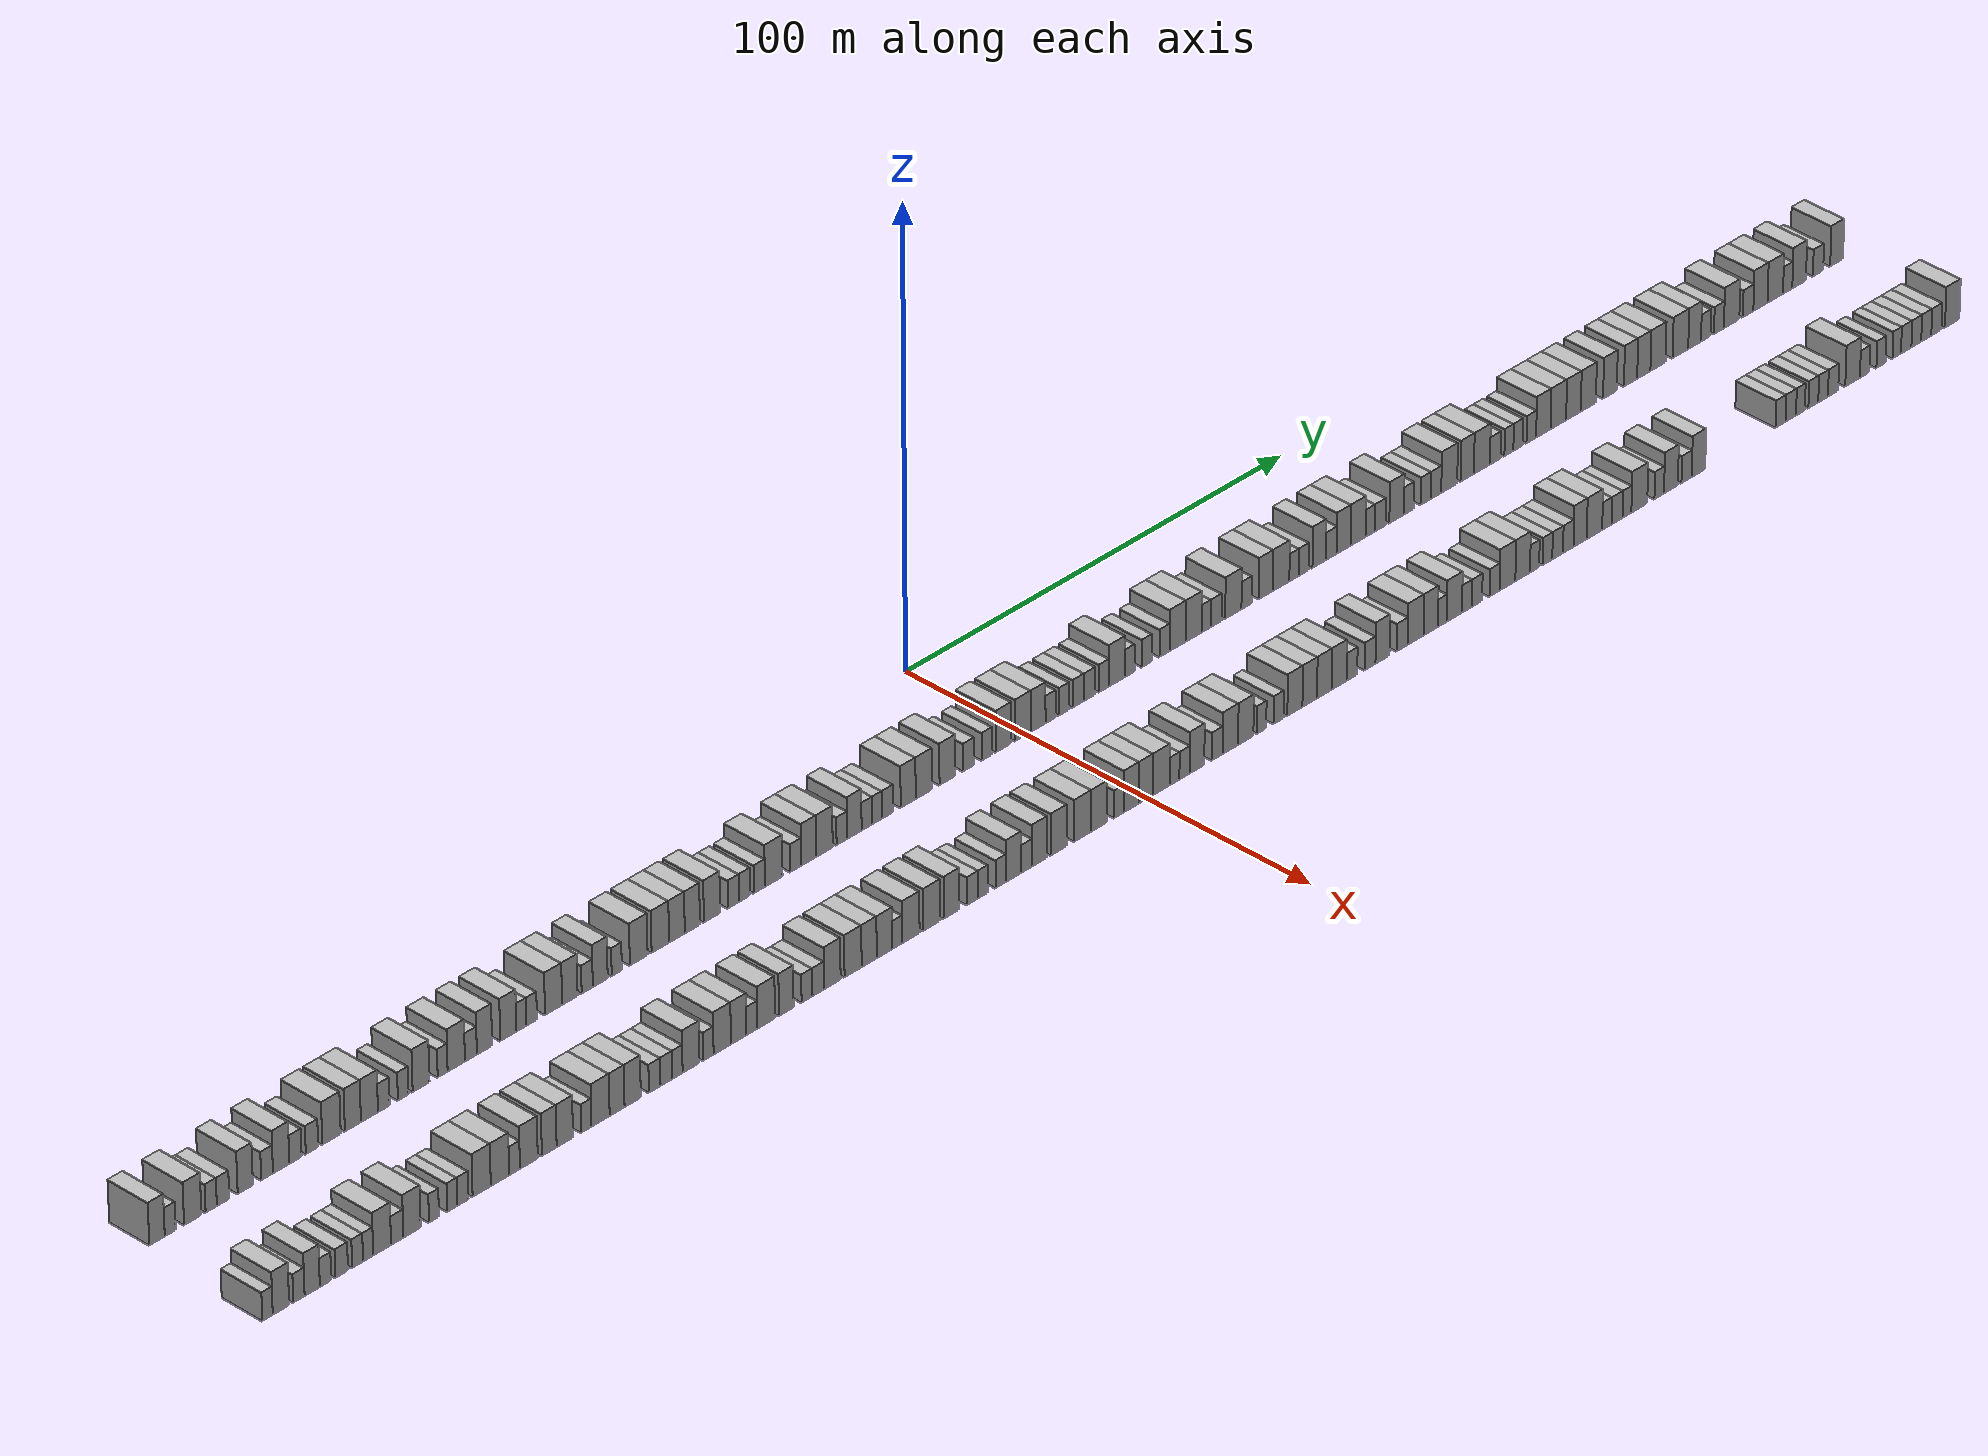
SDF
<sdf version="1.6">
 <world name="default">
  <scene>
   <sky><clouds><speed>12</speed></clouds></sky>
   <ambient>0.4 0.4 0.4 1</ambient>
   <background>0.7 0.7 0.7 1</background>
   <shadows>1</shadows>
  </scene>
  <gravity>0 0 -9.8066</gravity>
  <magnetic_field>6e-06 2.3e-05 -4.2e-05</magnetic_field>
  <physics default="0" name="default_physics" type="ode">
   <ode>
    <solver>
     <type>quick</type>
     <iters>10</iters>
     <sor>1.0</sor>
     <use_dynamic_moi_rescaling>0</use_dynamic_moi_rescaling>
    </solver>
    <constraints>
     <cfm>0</cfm>
     <erp>0.2</erp>
     <contact_max_correcting_vel>100</contact_max_correcting_vel>
     <contact_surface_layer>0.001</contact_surface_layer>
    </constraints>
   </ode>
   <max_step_size>0.004</max_step_size>
   <real_time_factor>1</real_time_factor>
   <real_time_update_rate>250</real_time_update_rate>
  </physics>
  <light name="sun" type="directional">
   <pose>0 0 10 0 0 0</pose>
   <diffuse>0.8 0.8 0.8 1</diffuse>
   <specular>0.2 0.2 0.2 1</specular>
   <attenuation>
    <range>1000</range>
    <constant>0.9</constant>
    <linear>0.01</linear>
    <quadratic>0.001</quadratic>
   </attenuation>
   <direction>-0.5 0.1 -0.9</direction>
  </light>
  <model name="building_1">
   <static>1</static>
   <pose>25.0000 -216.1763 0 0.000000 0.000000 0.000000</pose>
   <link name="link">
    <pose>0 0 4.50 0 0 0</pose>
    <collision name="collision"><geometry><box><size>10.0000 3.6474 9.0000</size></box></geometry></collision>
    <visual name="visual">
     <cast_shadows>0</cast_shadows>
     <geometry><box><size>10.0000 3.6474 9.0000</size></box></geometry>
     <material>
      <script>
       <uri>model://HANNAS_wall/materials/scripts</uri>
       <uri>model://HANNAS_wall/materials/textures</uri>
       <name>vrc/HANNAS_wall</name>
      </script>
     </material>
    </visual>
   </link>
  </model>
  <model name="building_2">
   <static>1</static>
   <pose>25.0000 -213.0599 0 0.000000 0.000000 0.000000</pose>
   <link name="link">
    <pose>0 0 3.00 0 0 0</pose>
    <collision name="collision"><geometry><box><size>10.0000 2.5855 6.0000</size></box></geometry></collision>
    <visual name="visual">
     <cast_shadows>0</cast_shadows>
     <geometry><box><size>10.0000 2.5855 6.0000</size></box></geometry>
     <material>
      <script>
       <uri>model://HANNAS_wall/materials/scripts</uri>
       <uri>model://HANNAS_wall/materials/textures</uri>
       <name>vrc/HANNAS_wall</name>
      </script>
     </material>
    </visual>
   </link>
  </model>
  <model name="building_3">
   <static>1</static>
   <pose>25.0000 -207.7158 0 0.000000 0.000000 0.000000</pose>
   <link name="link">
    <pose>0 0 4.50 0 0 0</pose>
    <collision name="collision"><geometry><box><size>10.0000 4.1027 9.0000</size></box></geometry></collision>
    <visual name="visual">
     <cast_shadows>0</cast_shadows>
     <geometry><box><size>10.0000 4.1027 9.0000</size></box></geometry>
     <material>
      <script>
       <uri>model://HANNAS_wall/materials/scripts</uri>
       <uri>model://HANNAS_wall/materials/textures</uri>
       <name>vrc/HANNAS_wall</name>
      </script>
     </material>
    </visual>
   </link>
  </model>
  <model name="building_4">
   <static>1</static>
   <pose>25.0000 -203.3240 0 0.000000 0.000000 0.000000</pose>
   <link name="link">
    <pose>0 0 3.00 0 0 0</pose>
    <collision name="collision"><geometry><box><size>10.0000 2.6808 6.0000</size></box></geometry></collision>
    <visual name="visual">
     <cast_shadows>0</cast_shadows>
     <geometry><box><size>10.0000 2.6808 6.0000</size></box></geometry>
     <material>
      <script>
       <uri>model://HANNAS_wall/materials/scripts</uri>
       <uri>model://HANNAS_wall/materials/textures</uri>
       <name>vrc/HANNAS_wall</name>
      </script>
     </material>
    </visual>
   </link>
  </model>
  <model name="building_5">
   <static>1</static>
   <pose>25.0000 -200.5025 0 0.000000 0.000000 0.000000</pose>
   <link name="link">
    <pose>0 0 3.00 0 0 0</pose>
    <collision name="collision"><geometry><box><size>10.0000 2.9622 6.0000</size></box></geometry></collision>
    <visual name="visual">
     <cast_shadows>0</cast_shadows>
     <geometry><box><size>10.0000 2.9622 6.0000</size></box></geometry>
     <material>
      <script>
       <uri>model://HANNAS_wall/materials/scripts</uri>
       <uri>model://HANNAS_wall/materials/textures</uri>
       <name>vrc/HANNAS_wall</name>
      </script>
     </material>
    </visual>
   </link>
  </model>
  <model name="building_6">
   <static>1</static>
   <pose>25.0000 -195.2018 0 0.000000 0.000000 0.000000</pose>
   <link name="link">
    <pose>0 0 4.50 0 0 0</pose>
    <collision name="collision"><geometry><box><size>10.0000 3.6391 9.0000</size></box></geometry></collision>
    <visual name="visual">
     <cast_shadows>0</cast_shadows>
     <geometry><box><size>10.0000 3.6391 9.0000</size></box></geometry>
     <material>
      <script>
       <uri>model://HANNAS_wall/materials/scripts</uri>
       <uri>model://HANNAS_wall/materials/textures</uri>
       <name>vrc/HANNAS_wall</name>
      </script>
     </material>
    </visual>
   </link>
  </model>
  <model name="building_7">
   <static>1</static>
   <pose>25.0000 -189.9766 0 0.000000 0.000000 0.000000</pose>
   <link name="link">
    <pose>0 0 3.00 0 0 0</pose>
    <collision name="collision"><geometry><box><size>10.0000 2.8114 6.0000</size></box></geometry></collision>
    <visual name="visual">
     <cast_shadows>0</cast_shadows>
     <geometry><box><size>10.0000 2.8114 6.0000</size></box></geometry>
     <material>
      <script>
       <uri>model://HANNAS_wall/materials/scripts</uri>
       <uri>model://HANNAS_wall/materials/textures</uri>
       <name>vrc/HANNAS_wall</name>
      </script>
     </material>
    </visual>
   </link>
  </model>
  <model name="building_8">
   <static>1</static>
   <pose>25.0000 -186.6073 0 0.000000 0.000000 0.000000</pose>
   <link name="link">
    <pose>0 0 4.50 0 0 0</pose>
    <collision name="collision"><geometry><box><size>10.0000 3.9271 9.0000</size></box></geometry></collision>
    <visual name="visual">
     <cast_shadows>0</cast_shadows>
     <geometry><box><size>10.0000 3.9271 9.0000</size></box></geometry>
     <material>
      <script>
       <uri>model://HANNAS_wall/materials/scripts</uri>
       <uri>model://HANNAS_wall/materials/textures</uri>
       <name>vrc/HANNAS_wall</name>
      </script>
     </material>
    </visual>
   </link>
  </model>
  <model name="building_9">
   <static>1</static>
   <pose>25.0000 -183.1718 0 0.000000 0.000000 0.000000</pose>
   <link name="link">
    <pose>0 0 3.00 0 0 0</pose>
    <collision name="collision"><geometry><box><size>10.0000 2.9438 6.0000</size></box></geometry></collision>
    <visual name="visual">
     <cast_shadows>0</cast_shadows>
     <geometry><box><size>10.0000 2.9438 6.0000</size></box></geometry>
     <material>
      <script>
       <uri>model://HANNAS_wall/materials/scripts</uri>
       <uri>model://HANNAS_wall/materials/textures</uri>
       <name>vrc/HANNAS_wall</name>
      </script>
     </material>
    </visual>
   </link>
  </model>
  <model name="building_10">
   <static>1</static>
   <pose>25.0000 -179.2069 0 0.000000 0.000000 0.000000</pose>
   <link name="link">
    <pose>0 0 3.00 0 0 0</pose>
    <collision name="collision"><geometry><box><size>10.0000 2.9862 6.0000</size></box></geometry></collision>
    <visual name="visual">
     <cast_shadows>0</cast_shadows>
     <geometry><box><size>10.0000 2.9862 6.0000</size></box></geometry>
     <material>
      <script>
       <uri>model://HANNAS_wall/materials/scripts</uri>
       <uri>model://HANNAS_wall/materials/textures</uri>
       <name>vrc/HANNAS_wall</name>
      </script>
     </material>
    </visual>
   </link>
  </model>
  <model name="building_11">
   <static>1</static>
   <pose>25.0000 -174.4941 0 0.000000 0.000000 0.000000</pose>
   <link name="link">
    <pose>0 0 4.50 0 0 0</pose>
    <collision name="collision"><geometry><box><size>10.0000 4.4394 9.0000</size></box></geometry></collision>
    <visual name="visual">
     <cast_shadows>0</cast_shadows>
     <geometry><box><size>10.0000 4.4394 9.0000</size></box></geometry>
     <material>
      <script>
       <uri>model://HANNAS_wall/materials/scripts</uri>
       <uri>model://HANNAS_wall/materials/textures</uri>
       <name>vrc/HANNAS_wall</name>
      </script>
     </material>
    </visual>
   </link>
  </model>
  <model name="building_12">
   <static>1</static>
   <pose>25.0000 -169.3286 0 0.000000 0.000000 0.000000</pose>
   <link name="link">
    <pose>0 0 4.50 0 0 0</pose>
    <collision name="collision"><geometry><box><size>10.0000 3.8914 9.0000</size></box></geometry></collision>
    <visual name="visual">
     <cast_shadows>0</cast_shadows>
     <geometry><box><size>10.0000 3.8914 9.0000</size></box></geometry>
     <material>
      <script>
       <uri>model://HANNAS_wall/materials/scripts</uri>
       <uri>model://HANNAS_wall/materials/textures</uri>
       <name>vrc/HANNAS_wall</name>
      </script>
     </material>
    </visual>
   </link>
  </model>
  <model name="building_13">
   <static>1</static>
   <pose>25.0000 -165.3194 0 0.000000 0.000000 0.000000</pose>
   <link name="link">
    <pose>0 0 4.50 0 0 0</pose>
    <collision name="collision"><geometry><box><size>10.0000 4.1270 9.0000</size></box></geometry></collision>
    <visual name="visual">
     <cast_shadows>0</cast_shadows>
     <geometry><box><size>10.0000 4.1270 9.0000</size></box></geometry>
     <material>
      <script>
       <uri>model://HANNAS_wall/materials/scripts</uri>
       <uri>model://HANNAS_wall/materials/textures</uri>
       <name>vrc/HANNAS_wall</name>
      </script>
     </material>
    </visual>
   </link>
  </model>
  <model name="building_14">
   <static>1</static>
   <pose>25.0000 -161.8414 0 0.000000 0.000000 0.000000</pose>
   <link name="link">
    <pose>0 0 3.00 0 0 0</pose>
    <collision name="collision"><geometry><box><size>10.0000 2.8291 6.0000</size></box></geometry></collision>
    <visual name="visual">
     <cast_shadows>0</cast_shadows>
     <geometry><box><size>10.0000 2.8291 6.0000</size></box></geometry>
     <material>
      <script>
       <uri>model://HANNAS_wall/materials/scripts</uri>
       <uri>model://HANNAS_wall/materials/textures</uri>
       <name>vrc/HANNAS_wall</name>
      </script>
     </material>
    </visual>
   </link>
  </model>
  <model name="building_15">
   <static>1</static>
   <pose>25.0000 -157.1286 0 0.000000 0.000000 0.000000</pose>
   <link name="link">
    <pose>0 0 3.00 0 0 0</pose>
    <collision name="collision"><geometry><box><size>10.0000 2.5964 6.0000</size></box></geometry></collision>
    <visual name="visual">
     <cast_shadows>0</cast_shadows>
     <geometry><box><size>10.0000 2.5964 6.0000</size></box></geometry>
     <material>
      <script>
       <uri>model://HANNAS_wall/materials/scripts</uri>
       <uri>model://HANNAS_wall/materials/textures</uri>
       <name>vrc/HANNAS_wall</name>
      </script>
     </material>
    </visual>
   </link>
  </model>
  <model name="building_16">
   <static>1</static>
   <pose>25.0000 -152.7794 0 0.000000 0.000000 0.000000</pose>
   <link name="link">
    <pose>0 0 4.50 0 0 0</pose>
    <collision name="collision"><geometry><box><size>10.0000 4.1021 9.0000</size></box></geometry></collision>
    <visual name="visual">
     <cast_shadows>0</cast_shadows>
     <geometry><box><size>10.0000 4.1021 9.0000</size></box></geometry>
     <material>
      <script>
       <uri>model://HANNAS_wall/materials/scripts</uri>
       <uri>model://HANNAS_wall/materials/textures</uri>
       <name>vrc/HANNAS_wall</name>
      </script>
     </material>
    </visual>
   </link>
  </model>
  <model name="building_17">
   <static>1</static>
   <pose>25.0000 -147.5157 0 0.000000 0.000000 0.000000</pose>
   <link name="link">
    <pose>0 0 3.00 0 0 0</pose>
    <collision name="collision"><geometry><box><size>10.0000 2.4252 6.0000</size></box></geometry></collision>
    <visual name="visual">
     <cast_shadows>0</cast_shadows>
     <geometry><box><size>10.0000 2.4252 6.0000</size></box></geometry>
     <material>
      <script>
       <uri>model://HANNAS_wall/materials/scripts</uri>
       <uri>model://HANNAS_wall/materials/textures</uri>
       <name>vrc/HANNAS_wall</name>
      </script>
     </material>
    </visual>
   </link>
  </model>
  <model name="building_18">
   <static>1</static>
   <pose>25.0000 -144.1805 0 0.000000 0.000000 0.000000</pose>
   <link name="link">
    <pose>0 0 4.50 0 0 0</pose>
    <collision name="collision"><geometry><box><size>10.0000 4.2452 9.0000</size></box></geometry></collision>
    <visual name="visual">
     <cast_shadows>0</cast_shadows>
     <geometry><box><size>10.0000 4.2452 9.0000</size></box></geometry>
     <material>
      <script>
       <uri>model://HANNAS_wall/materials/scripts</uri>
       <uri>model://HANNAS_wall/materials/textures</uri>
       <name>vrc/HANNAS_wall</name>
      </script>
     </material>
    </visual>
   </link>
  </model>
  <model name="building_19">
   <static>1</static>
   <pose>25.0000 -140.5968 0 0.000000 0.000000 0.000000</pose>
   <link name="link">
    <pose>0 0 3.00 0 0 0</pose>
    <collision name="collision"><geometry><box><size>10.0000 2.9223 6.0000</size></box></geometry></collision>
    <visual name="visual">
     <cast_shadows>0</cast_shadows>
     <geometry><box><size>10.0000 2.9223 6.0000</size></box></geometry>
     <material>
      <script>
       <uri>model://HANNAS_wall/materials/scripts</uri>
       <uri>model://HANNAS_wall/materials/textures</uri>
       <name>vrc/HANNAS_wall</name>
      </script>
     </material>
    </visual>
   </link>
  </model>
  <model name="building_20">
   <static>1</static>
   <pose>25.0000 -137.2635 0 0.000000 0.000000 0.000000</pose>
   <link name="link">
    <pose>0 0 4.50 0 0 0</pose>
    <collision name="collision"><geometry><box><size>10.0000 3.7443 9.0000</size></box></geometry></collision>
    <visual name="visual">
     <cast_shadows>0</cast_shadows>
     <geometry><box><size>10.0000 3.7443 9.0000</size></box></geometry>
     <material>
      <script>
       <uri>model://HANNAS_wall/materials/scripts</uri>
       <uri>model://HANNAS_wall/materials/textures</uri>
       <name>vrc/HANNAS_wall</name>
      </script>
     </material>
    </visual>
   </link>
  </model>
  <model name="building_21">
   <static>1</static>
   <pose>25.0000 -131.4037 0 0.000000 0.000000 0.000000</pose>
   <link name="link">
    <pose>0 0 4.50 0 0 0</pose>
    <collision name="collision"><geometry><box><size>10.0000 3.9755 9.0000</size></box></geometry></collision>
    <visual name="visual">
     <cast_shadows>0</cast_shadows>
     <geometry><box><size>10.0000 3.9755 9.0000</size></box></geometry>
     <material>
      <script>
       <uri>model://HANNAS_wall/materials/scripts</uri>
       <uri>model://HANNAS_wall/materials/textures</uri>
       <name>vrc/HANNAS_wall</name>
      </script>
     </material>
    </visual>
   </link>
  </model>
  <model name="building_22">
   <static>1</static>
   <pose>25.0000 -128.1757 0 0.000000 0.000000 0.000000</pose>
   <link name="link">
    <pose>0 0 3.00 0 0 0</pose>
    <collision name="collision"><geometry><box><size>10.0000 2.4804 6.0000</size></box></geometry></collision>
    <visual name="visual">
     <cast_shadows>0</cast_shadows>
     <geometry><box><size>10.0000 2.4804 6.0000</size></box></geometry>
     <material>
      <script>
       <uri>model://HANNAS_wall/materials/scripts</uri>
       <uri>model://HANNAS_wall/materials/textures</uri>
       <name>vrc/HANNAS_wall</name>
      </script>
     </material>
    </visual>
   </link>
  </model>
  <model name="building_23">
   <static>1</static>
   <pose>25.0000 -125.6477 0 0.000000 0.000000 0.000000</pose>
   <link name="link">
    <pose>0 0 3.00 0 0 0</pose>
    <collision name="collision"><geometry><box><size>10.0000 2.5757 6.0000</size></box></geometry></collision>
    <visual name="visual">
     <cast_shadows>0</cast_shadows>
     <geometry><box><size>10.0000 2.5757 6.0000</size></box></geometry>
     <material>
      <script>
       <uri>model://HANNAS_wall/materials/scripts</uri>
       <uri>model://HANNAS_wall/materials/textures</uri>
       <name>vrc/HANNAS_wall</name>
      </script>
     </material>
    </visual>
   </link>
  </model>
  <model name="building_24">
   <static>1</static>
   <pose>25.0000 -120.2416 0 0.000000 0.000000 0.000000</pose>
   <link name="link">
    <pose>0 0 4.50 0 0 0</pose>
    <collision name="collision"><geometry><box><size>10.0000 4.2365 9.0000</size></box></geometry></collision>
    <visual name="visual">
     <cast_shadows>0</cast_shadows>
     <geometry><box><size>10.0000 4.2365 9.0000</size></box></geometry>
     <material>
      <script>
       <uri>model://HANNAS_wall/materials/scripts</uri>
       <uri>model://HANNAS_wall/materials/textures</uri>
       <name>vrc/HANNAS_wall</name>
      </script>
     </material>
    </visual>
   </link>
  </model>
  <model name="building_25">
   <static>1</static>
   <pose>25.0000 -116.2081 0 0.000000 0.000000 0.000000</pose>
   <link name="link">
    <pose>0 0 4.50 0 0 0</pose>
    <collision name="collision"><geometry><box><size>10.0000 3.8305 9.0000</size></box></geometry></collision>
    <visual name="visual">
     <cast_shadows>0</cast_shadows>
     <geometry><box><size>10.0000 3.8305 9.0000</size></box></geometry>
     <material>
      <script>
       <uri>model://HANNAS_wall/materials/scripts</uri>
       <uri>model://HANNAS_wall/materials/textures</uri>
       <name>vrc/HANNAS_wall</name>
      </script>
     </material>
    </visual>
   </link>
  </model>
  <model name="building_26">
   <static>1</static>
   <pose>25.0000 -111.9049 0 0.000000 0.000000 0.000000</pose>
   <link name="link">
    <pose>0 0 3.00 0 0 0</pose>
    <collision name="collision"><geometry><box><size>10.0000 2.7758 6.0000</size></box></geometry></collision>
    <visual name="visual">
     <cast_shadows>0</cast_shadows>
     <geometry><box><size>10.0000 2.7758 6.0000</size></box></geometry>
     <material>
      <script>
       <uri>model://HANNAS_wall/materials/scripts</uri>
       <uri>model://HANNAS_wall/materials/textures</uri>
       <name>vrc/HANNAS_wall</name>
      </script>
     </material>
    </visual>
   </link>
  </model>
  <model name="building_27">
   <static>1</static>
   <pose>25.0000 -108.6695 0 0.000000 0.000000 0.000000</pose>
   <link name="link">
    <pose>0 0 4.50 0 0 0</pose>
    <collision name="collision"><geometry><box><size>10.0000 3.6949 9.0000</size></box></geometry></collision>
    <visual name="visual">
     <cast_shadows>0</cast_shadows>
     <geometry><box><size>10.0000 3.6949 9.0000</size></box></geometry>
     <material>
      <script>
       <uri>model://HANNAS_wall/materials/scripts</uri>
       <uri>model://HANNAS_wall/materials/textures</uri>
       <name>vrc/HANNAS_wall</name>
      </script>
     </material>
    </visual>
   </link>
  </model>
  <model name="building_28">
   <static>1</static>
   <pose>25.0000 -104.5605 0 0.000000 0.000000 0.000000</pose>
   <link name="link">
    <pose>0 0 3.00 0 0 0</pose>
    <collision name="collision"><geometry><box><size>10.0000 2.5230 6.0000</size></box></geometry></collision>
    <visual name="visual">
     <cast_shadows>0</cast_shadows>
     <geometry><box><size>10.0000 2.5230 6.0000</size></box></geometry>
     <material>
      <script>
       <uri>model://HANNAS_wall/materials/scripts</uri>
       <uri>model://HANNAS_wall/materials/textures</uri>
       <name>vrc/HANNAS_wall</name>
      </script>
     </material>
    </visual>
   </link>
  </model>
  <model name="building_29">
   <static>1</static>
   <pose>25.0000 -99.0794 0 0.000000 0.000000 0.000000</pose>
   <link name="link">
    <pose>0 0 4.50 0 0 0</pose>
    <collision name="collision"><geometry><box><size>10.0000 4.4393 9.0000</size></box></geometry></collision>
    <visual name="visual">
     <cast_shadows>0</cast_shadows>
     <geometry><box><size>10.0000 4.4393 9.0000</size></box></geometry>
     <material>
      <script>
       <uri>model://HANNAS_wall/materials/scripts</uri>
       <uri>model://HANNAS_wall/materials/textures</uri>
       <name>vrc/HANNAS_wall</name>
      </script>
     </material>
    </visual>
   </link>
  </model>
  <model name="building_30">
   <static>1</static>
   <pose>25.0000 -93.6761 0 0.000000 0.000000 0.000000</pose>
   <link name="link">
    <pose>0 0 4.50 0 0 0</pose>
    <collision name="collision"><geometry><box><size>10.0000 4.3673 9.0000</size></box></geometry></collision>
    <visual name="visual">
     <cast_shadows>0</cast_shadows>
     <geometry><box><size>10.0000 4.3673 9.0000</size></box></geometry>
     <material>
      <script>
       <uri>model://HANNAS_wall/materials/scripts</uri>
       <uri>model://HANNAS_wall/materials/textures</uri>
       <name>vrc/HANNAS_wall</name>
      </script>
     </material>
    </visual>
   </link>
  </model>
  <model name="building_31">
   <static>1</static>
   <pose>25.0000 -89.5185 0 0.000000 0.000000 0.000000</pose>
   <link name="link">
    <pose>0 0 4.50 0 0 0</pose>
    <collision name="collision"><geometry><box><size>10.0000 3.9477 9.0000</size></box></geometry></collision>
    <visual name="visual">
     <cast_shadows>0</cast_shadows>
     <geometry><box><size>10.0000 3.9477 9.0000</size></box></geometry>
     <material>
      <script>
       <uri>model://HANNAS_wall/materials/scripts</uri>
       <uri>model://HANNAS_wall/materials/textures</uri>
       <name>vrc/HANNAS_wall</name>
      </script>
     </material>
    </visual>
   </link>
  </model>
  <model name="building_32">
   <static>1</static>
   <pose>25.0000 -85.6427 0 0.000000 0.000000 0.000000</pose>
   <link name="link">
    <pose>0 0 4.50 0 0 0</pose>
    <collision name="collision"><geometry><box><size>10.0000 3.8040 9.0000</size></box></geometry></collision>
    <visual name="visual">
     <cast_shadows>0</cast_shadows>
     <geometry><box><size>10.0000 3.8040 9.0000</size></box></geometry>
     <material>
      <script>
       <uri>model://HANNAS_wall/materials/scripts</uri>
       <uri>model://HANNAS_wall/materials/textures</uri>
       <name>vrc/HANNAS_wall</name>
      </script>
     </material>
    </visual>
   </link>
  </model>
  <model name="building_33">
   <static>1</static>
   <pose>25.0000 -80.7029 0 0.000000 0.000000 0.000000</pose>
   <link name="link">
    <pose>0 0 4.50 0 0 0</pose>
    <collision name="collision"><geometry><box><size>10.0000 4.0755 9.0000</size></box></geometry></collision>
    <visual name="visual">
     <cast_shadows>0</cast_shadows>
     <geometry><box><size>10.0000 4.0755 9.0000</size></box></geometry>
     <material>
      <script>
       <uri>model://HANNAS_wall/materials/scripts</uri>
       <uri>model://HANNAS_wall/materials/textures</uri>
       <name>vrc/HANNAS_wall</name>
      </script>
     </material>
    </visual>
   </link>
  </model>
  <model name="building_34">
   <static>1</static>
   <pose>25.0000 -75.2539 0 0.000000 0.000000 0.000000</pose>
   <link name="link">
    <pose>0 0 3.00 0 0 0</pose>
    <collision name="collision"><geometry><box><size>10.0000 2.8225 6.0000</size></box></geometry></collision>
    <visual name="visual">
     <cast_shadows>0</cast_shadows>
     <geometry><box><size>10.0000 2.8225 6.0000</size></box></geometry>
     <material>
      <script>
       <uri>model://HANNAS_wall/materials/scripts</uri>
       <uri>model://HANNAS_wall/materials/textures</uri>
       <name>vrc/HANNAS_wall</name>
      </script>
     </material>
    </visual>
   </link>
  </model>
  <model name="building_35">
   <static>1</static>
   <pose>25.0000 -72.4639 0 0.000000 0.000000 0.000000</pose>
   <link name="link">
    <pose>0 0 3.00 0 0 0</pose>
    <collision name="collision"><geometry><box><size>10.0000 2.7576 6.0000</size></box></geometry></collision>
    <visual name="visual">
     <cast_shadows>0</cast_shadows>
     <geometry><box><size>10.0000 2.7576 6.0000</size></box></geometry>
     <material>
      <script>
       <uri>model://HANNAS_wall/materials/scripts</uri>
       <uri>model://HANNAS_wall/materials/textures</uri>
       <name>vrc/HANNAS_wall</name>
      </script>
     </material>
    </visual>
   </link>
  </model>
  <model name="building_36">
   <static>1</static>
   <pose>25.0000 -68.7085 0 0.000000 0.000000 0.000000</pose>
   <link name="link">
    <pose>0 0 3.00 0 0 0</pose>
    <collision name="collision"><geometry><box><size>10.0000 2.7532 6.0000</size></box></geometry></collision>
    <visual name="visual">
     <cast_shadows>0</cast_shadows>
     <geometry><box><size>10.0000 2.7532 6.0000</size></box></geometry>
     <material>
      <script>
       <uri>model://HANNAS_wall/materials/scripts</uri>
       <uri>model://HANNAS_wall/materials/textures</uri>
       <name>vrc/HANNAS_wall</name>
      </script>
     </material>
    </visual>
   </link>
  </model>
  <model name="building_37">
   <static>1</static>
   <pose>25.0000 -65.0946 0 0.000000 0.000000 0.000000</pose>
   <link name="link">
    <pose>0 0 4.50 0 0 0</pose>
    <collision name="collision"><geometry><box><size>10.0000 4.4745 9.0000</size></box></geometry></collision>
    <visual name="visual">
     <cast_shadows>0</cast_shadows>
     <geometry><box><size>10.0000 4.4745 9.0000</size></box></geometry>
     <material>
      <script>
       <uri>model://HANNAS_wall/materials/scripts</uri>
       <uri>model://HANNAS_wall/materials/textures</uri>
       <name>vrc/HANNAS_wall</name>
      </script>
     </material>
    </visual>
   </link>
  </model>
  <model name="building_38">
   <static>1</static>
   <pose>25.0000 -59.4765 0 0.000000 0.000000 0.000000</pose>
   <link name="link">
    <pose>0 0 3.00 0 0 0</pose>
    <collision name="collision"><geometry><box><size>10.0000 2.7617 6.0000</size></box></geometry></collision>
    <visual name="visual">
     <cast_shadows>0</cast_shadows>
     <geometry><box><size>10.0000 2.7617 6.0000</size></box></geometry>
     <material>
      <script>
       <uri>model://HANNAS_wall/materials/scripts</uri>
       <uri>model://HANNAS_wall/materials/textures</uri>
       <name>vrc/HANNAS_wall</name>
      </script>
     </material>
    </visual>
   </link>
  </model>
  <model name="building_39">
   <static>1</static>
   <pose>25.0000 -56.2175 0 0.000000 0.000000 0.000000</pose>
   <link name="link">
    <pose>0 0 4.50 0 0 0</pose>
    <collision name="collision"><geometry><box><size>10.0000 3.7563 9.0000</size></box></geometry></collision>
    <visual name="visual">
     <cast_shadows>0</cast_shadows>
     <geometry><box><size>10.0000 3.7563 9.0000</size></box></geometry>
     <material>
      <script>
       <uri>model://HANNAS_wall/materials/scripts</uri>
       <uri>model://HANNAS_wall/materials/textures</uri>
       <name>vrc/HANNAS_wall</name>
      </script>
     </material>
    </visual>
   </link>
  </model>
  <model name="building_40">
   <static>1</static>
   <pose>25.0000 -52.2146 0 0.000000 0.000000 0.000000</pose>
   <link name="link">
    <pose>0 0 4.50 0 0 0</pose>
    <collision name="collision"><geometry><box><size>10.0000 4.2497 9.0000</size></box></geometry></collision>
    <visual name="visual">
     <cast_shadows>0</cast_shadows>
     <geometry><box><size>10.0000 4.2497 9.0000</size></box></geometry>
     <material>
      <script>
       <uri>model://HANNAS_wall/materials/scripts</uri>
       <uri>model://HANNAS_wall/materials/textures</uri>
       <name>vrc/HANNAS_wall</name>
      </script>
     </material>
    </visual>
   </link>
  </model>
  <model name="building_41">
   <static>1</static>
   <pose>25.0000 -47.7446 0 0.000000 0.000000 0.000000</pose>
   <link name="link">
    <pose>0 0 3.00 0 0 0</pose>
    <collision name="collision"><geometry><box><size>10.0000 2.6902 6.0000</size></box></geometry></collision>
    <visual name="visual">
     <cast_shadows>0</cast_shadows>
     <geometry><box><size>10.0000 2.6902 6.0000</size></box></geometry>
     <material>
      <script>
       <uri>model://HANNAS_wall/materials/scripts</uri>
       <uri>model://HANNAS_wall/materials/textures</uri>
       <name>vrc/HANNAS_wall</name>
      </script>
     </material>
    </visual>
   </link>
  </model>
  <model name="building_42">
   <static>1</static>
   <pose>25.0000 -44.5399 0 0.000000 0.000000 0.000000</pose>
   <link name="link">
    <pose>0 0 4.50 0 0 0</pose>
    <collision name="collision"><geometry><box><size>10.0000 3.7191 9.0000</size></box></geometry></collision>
    <visual name="visual">
     <cast_shadows>0</cast_shadows>
     <geometry><box><size>10.0000 3.7191 9.0000</size></box></geometry>
     <material>
      <script>
       <uri>model://HANNAS_wall/materials/scripts</uri>
       <uri>model://HANNAS_wall/materials/textures</uri>
       <name>vrc/HANNAS_wall</name>
      </script>
     </material>
    </visual>
   </link>
  </model>
  <model name="building_43">
   <static>1</static>
   <pose>25.0000 -41.2943 0 0.000000 0.000000 0.000000</pose>
   <link name="link">
    <pose>0 0 3.00 0 0 0</pose>
    <collision name="collision"><geometry><box><size>10.0000 2.7721 6.0000</size></box></geometry></collision>
    <visual name="visual">
     <cast_shadows>0</cast_shadows>
     <geometry><box><size>10.0000 2.7721 6.0000</size></box></geometry>
     <material>
      <script>
       <uri>model://HANNAS_wall/materials/scripts</uri>
       <uri>model://HANNAS_wall/materials/textures</uri>
       <name>vrc/HANNAS_wall</name>
      </script>
     </material>
    </visual>
   </link>
  </model>
  <model name="building_44">
   <static>1</static>
   <pose>25.0000 -38.6883 0 0.000000 0.000000 0.000000</pose>
   <link name="link">
    <pose>0 0 3.00 0 0 0</pose>
    <collision name="collision"><geometry><box><size>10.0000 2.4399 6.0000</size></box></geometry></collision>
    <visual name="visual">
     <cast_shadows>0</cast_shadows>
     <geometry><box><size>10.0000 2.4399 6.0000</size></box></geometry>
     <material>
      <script>
       <uri>model://HANNAS_wall/materials/scripts</uri>
       <uri>model://HANNAS_wall/materials/textures</uri>
       <name>vrc/HANNAS_wall</name>
      </script>
     </material>
    </visual>
   </link>
  </model>
  <model name="building_45">
   <static>1</static>
   <pose>25.0000 -36.0601 0 0.000000 0.000000 0.000000</pose>
   <link name="link">
    <pose>0 0 3.00 0 0 0</pose>
    <collision name="collision"><geometry><box><size>10.0000 2.8165 6.0000</size></box></geometry></collision>
    <visual name="visual">
     <cast_shadows>0</cast_shadows>
     <geometry><box><size>10.0000 2.8165 6.0000</size></box></geometry>
     <material>
      <script>
       <uri>model://HANNAS_wall/materials/scripts</uri>
       <uri>model://HANNAS_wall/materials/textures</uri>
       <name>vrc/HANNAS_wall</name>
      </script>
     </material>
    </visual>
   </link>
  </model>
  <model name="building_46">
   <static>1</static>
   <pose>25.0000 -30.7179 0 0.000000 0.000000 0.000000</pose>
   <link name="link">
    <pose>0 0 4.50 0 0 0</pose>
    <collision name="collision"><geometry><box><size>10.0000 3.8680 9.0000</size></box></geometry></collision>
    <visual name="visual">
     <cast_shadows>0</cast_shadows>
     <geometry><box><size>10.0000 3.8680 9.0000</size></box></geometry>
     <material>
      <script>
       <uri>model://HANNAS_wall/materials/scripts</uri>
       <uri>model://HANNAS_wall/materials/textures</uri>
       <name>vrc/HANNAS_wall</name>
      </script>
     </material>
    </visual>
   </link>
  </model>
  <model name="building_47">
   <static>1</static>
   <pose>25.0000 -26.7007 0 0.000000 0.000000 0.000000</pose>
   <link name="link">
    <pose>0 0 4.50 0 0 0</pose>
    <collision name="collision"><geometry><box><size>10.0000 4.1663 9.0000</size></box></geometry></collision>
    <visual name="visual">
     <cast_shadows>0</cast_shadows>
     <geometry><box><size>10.0000 4.1663 9.0000</size></box></geometry>
     <material>
      <script>
       <uri>model://HANNAS_wall/materials/scripts</uri>
       <uri>model://HANNAS_wall/materials/textures</uri>
       <name>vrc/HANNAS_wall</name>
      </script>
     </material>
    </visual>
   </link>
  </model>
  <model name="building_48">
   <static>1</static>
   <pose>25.0000 -20.5544 0 0.000000 0.000000 0.000000</pose>
   <link name="link">
    <pose>0 0 4.50 0 0 0</pose>
    <collision name="collision"><geometry><box><size>10.0000 4.1264 9.0000</size></box></geometry></collision>
    <visual name="visual">
     <cast_shadows>0</cast_shadows>
     <geometry><box><size>10.0000 4.1264 9.0000</size></box></geometry>
     <material>
      <script>
       <uri>model://HANNAS_wall/materials/scripts</uri>
       <uri>model://HANNAS_wall/materials/textures</uri>
       <name>vrc/HANNAS_wall</name>
      </script>
     </material>
    </visual>
   </link>
  </model>
  <model name="building_49">
   <static>1</static>
   <pose>25.0000 -15.0626 0 0.000000 0.000000 0.000000</pose>
   <link name="link">
    <pose>0 0 3.00 0 0 0</pose>
    <collision name="collision"><geometry><box><size>10.0000 2.8571 6.0000</size></box></geometry></collision>
    <visual name="visual">
     <cast_shadows>0</cast_shadows>
     <geometry><box><size>10.0000 2.8571 6.0000</size></box></geometry>
     <material>
      <script>
       <uri>model://HANNAS_wall/materials/scripts</uri>
       <uri>model://HANNAS_wall/materials/textures</uri>
       <name>vrc/HANNAS_wall</name>
      </script>
     </material>
    </visual>
   </link>
  </model>
  <model name="building_50">
   <static>1</static>
   <pose>25.0000 -10.3037 0 0.000000 0.000000 0.000000</pose>
   <link name="link">
    <pose>0 0 3.00 0 0 0</pose>
    <collision name="collision"><geometry><box><size>10.0000 2.6608 6.0000</size></box></geometry></collision>
    <visual name="visual">
     <cast_shadows>0</cast_shadows>
     <geometry><box><size>10.0000 2.6608 6.0000</size></box></geometry>
     <material>
      <script>
       <uri>model://HANNAS_wall/materials/scripts</uri>
       <uri>model://HANNAS_wall/materials/textures</uri>
       <name>vrc/HANNAS_wall</name>
      </script>
     </material>
    </visual>
   </link>
  </model>
  <model name="building_51">
   <static>1</static>
   <pose>25.0000 -5.9813 0 0.000000 0.000000 0.000000</pose>
   <link name="link">
    <pose>0 0 4.50 0 0 0</pose>
    <collision name="collision"><geometry><box><size>10.0000 3.9838 9.0000</size></box></geometry></collision>
    <visual name="visual">
     <cast_shadows>0</cast_shadows>
     <geometry><box><size>10.0000 3.9838 9.0000</size></box></geometry>
     <material>
      <script>
       <uri>model://HANNAS_wall/materials/scripts</uri>
       <uri>model://HANNAS_wall/materials/textures</uri>
       <name>vrc/HANNAS_wall</name>
      </script>
     </material>
    </visual>
   </link>
  </model>
  <model name="building_52">
   <static>1</static>
   <pose>25.0000 -0.9367 0 0.000000 0.000000 0.000000</pose>
   <link name="link">
    <pose>0 0 4.50 0 0 0</pose>
    <collision name="collision"><geometry><box><size>10.0000 4.1054 9.0000</size></box></geometry></collision>
    <visual name="visual">
     <cast_shadows>0</cast_shadows>
     <geometry><box><size>10.0000 4.1054 9.0000</size></box></geometry>
     <material>
      <script>
       <uri>model://HANNAS_wall/materials/scripts</uri>
       <uri>model://HANNAS_wall/materials/textures</uri>
       <name>vrc/HANNAS_wall</name>
      </script>
     </material>
    </visual>
   </link>
  </model>
  <model name="building_53">
   <static>1</static>
   <pose>25.0000 3.0385 0 0.000000 0.000000 0.000000</pose>
   <link name="link">
    <pose>0 0 4.50 0 0 0</pose>
    <collision name="collision"><geometry><box><size>10.0000 3.8451 9.0000</size></box></geometry></collision>
    <visual name="visual">
     <cast_shadows>0</cast_shadows>
     <geometry><box><size>10.0000 3.8451 9.0000</size></box></geometry>
     <material>
      <script>
       <uri>model://HANNAS_wall/materials/scripts</uri>
       <uri>model://HANNAS_wall/materials/textures</uri>
       <name>vrc/HANNAS_wall</name>
      </script>
     </material>
    </visual>
   </link>
  </model>
  <model name="building_54">
   <static>1</static>
   <pose>25.0000 6.2718 0 0.000000 0.000000 0.000000</pose>
   <link name="link">
    <pose>0 0 3.00 0 0 0</pose>
    <collision name="collision"><geometry><box><size>10.0000 2.6216 6.0000</size></box></geometry></collision>
    <visual name="visual">
     <cast_shadows>0</cast_shadows>
     <geometry><box><size>10.0000 2.6216 6.0000</size></box></geometry>
     <material>
      <script>
       <uri>model://HANNAS_wall/materials/scripts</uri>
       <uri>model://HANNAS_wall/materials/textures</uri>
       <name>vrc/HANNAS_wall</name>
      </script>
     </material>
    </visual>
   </link>
  </model>
  <model name="building_55">
   <static>1</static>
   <pose>25.0000 9.8416 0 0.000000 0.000000 0.000000</pose>
   <link name="link">
    <pose>0 0 3.00 0 0 0</pose>
    <collision name="collision"><geometry><box><size>10.0000 2.5180 6.0000</size></box></geometry></collision>
    <visual name="visual">
     <cast_shadows>0</cast_shadows>
     <geometry><box><size>10.0000 2.5180 6.0000</size></box></geometry>
     <material>
      <script>
       <uri>model://HANNAS_wall/materials/scripts</uri>
       <uri>model://HANNAS_wall/materials/textures</uri>
       <name>vrc/HANNAS_wall</name>
      </script>
     </material>
    </visual>
   </link>
  </model>
  <model name="building_56">
   <static>1</static>
   <pose>25.0000 13.5956 0 0.000000 0.000000 0.000000</pose>
   <link name="link">
    <pose>0 0 3.00 0 0 0</pose>
    <collision name="collision"><geometry><box><size>10.0000 2.9900 6.0000</size></box></geometry></collision>
    <visual name="visual">
     <cast_shadows>0</cast_shadows>
     <geometry><box><size>10.0000 2.9900 6.0000</size></box></geometry>
     <material>
      <script>
       <uri>model://HANNAS_wall/materials/scripts</uri>
       <uri>model://HANNAS_wall/materials/textures</uri>
       <name>vrc/HANNAS_wall</name>
      </script>
     </material>
    </visual>
   </link>
  </model>
  <model name="building_57">
   <static>1</static>
   <pose>25.0000 16.5697 0 0.000000 0.000000 0.000000</pose>
   <link name="link">
    <pose>0 0 3.00 0 0 0</pose>
    <collision name="collision"><geometry><box><size>10.0000 2.9582 6.0000</size></box></geometry></collision>
    <visual name="visual">
     <cast_shadows>0</cast_shadows>
     <geometry><box><size>10.0000 2.9582 6.0000</size></box></geometry>
     <material>
      <script>
       <uri>model://HANNAS_wall/materials/scripts</uri>
       <uri>model://HANNAS_wall/materials/textures</uri>
       <name>vrc/HANNAS_wall</name>
      </script>
     </material>
    </visual>
   </link>
  </model>
  <model name="building_58">
   <static>1</static>
   <pose>25.0000 20.3652 0 0.000000 0.000000 0.000000</pose>
   <link name="link">
    <pose>0 0 3.00 0 0 0</pose>
    <collision name="collision"><geometry><box><size>10.0000 2.6328 6.0000</size></box></geometry></collision>
    <visual name="visual">
     <cast_shadows>0</cast_shadows>
     <geometry><box><size>10.0000 2.6328 6.0000</size></box></geometry>
     <material>
      <script>
       <uri>model://HANNAS_wall/materials/scripts</uri>
       <uri>model://HANNAS_wall/materials/textures</uri>
       <name>vrc/HANNAS_wall</name>
      </script>
     </material>
    </visual>
   </link>
  </model>
  <model name="building_59">
   <static>1</static>
   <pose>25.0000 23.7992 0 0.000000 0.000000 0.000000</pose>
   <link name="link">
    <pose>0 0 4.50 0 0 0</pose>
    <collision name="collision"><geometry><box><size>10.0000 4.2353 9.0000</size></box></geometry></collision>
    <visual name="visual">
     <cast_shadows>0</cast_shadows>
     <geometry><box><size>10.0000 4.2353 9.0000</size></box></geometry>
     <material>
      <script>
       <uri>model://HANNAS_wall/materials/scripts</uri>
       <uri>model://HANNAS_wall/materials/textures</uri>
       <name>vrc/HANNAS_wall</name>
      </script>
     </material>
    </visual>
   </link>
  </model>
  <model name="building_60">
   <static>1</static>
   <pose>25.0000 27.1506 0 0.000000 0.000000 0.000000</pose>
   <link name="link">
    <pose>0 0 3.00 0 0 0</pose>
    <collision name="collision"><geometry><box><size>10.0000 2.4674 6.0000</size></box></geometry></collision>
    <visual name="visual">
     <cast_shadows>0</cast_shadows>
     <geometry><box><size>10.0000 2.4674 6.0000</size></box></geometry>
     <material>
      <script>
       <uri>model://HANNAS_wall/materials/scripts</uri>
       <uri>model://HANNAS_wall/materials/textures</uri>
       <name>vrc/HANNAS_wall</name>
      </script>
     </material>
    </visual>
   </link>
  </model>
  <model name="building_61">
   <static>1</static>
   <pose>25.0000 31.7024 0 0.000000 0.000000 0.000000</pose>
   <link name="link">
    <pose>0 0 3.00 0 0 0</pose>
    <collision name="collision"><geometry><box><size>10.0000 2.6361 6.0000</size></box></geometry></collision>
    <visual name="visual">
     <cast_shadows>0</cast_shadows>
     <geometry><box><size>10.0000 2.6361 6.0000</size></box></geometry>
     <material>
      <script>
       <uri>model://HANNAS_wall/materials/scripts</uri>
       <uri>model://HANNAS_wall/materials/textures</uri>
       <name>vrc/HANNAS_wall</name>
      </script>
     </material>
    </visual>
   </link>
  </model>
  <model name="building_62">
   <static>1</static>
   <pose>25.0000 36.3706 0 0.000000 0.000000 0.000000</pose>
   <link name="link">
    <pose>0 0 3.00 0 0 0</pose>
    <collision name="collision"><geometry><box><size>10.0000 2.7004 6.0000</size></box></geometry></collision>
    <visual name="visual">
     <cast_shadows>0</cast_shadows>
     <geometry><box><size>10.0000 2.7004 6.0000</size></box></geometry>
     <material>
      <script>
       <uri>model://HANNAS_wall/materials/scripts</uri>
       <uri>model://HANNAS_wall/materials/textures</uri>
       <name>vrc/HANNAS_wall</name>
      </script>
     </material>
    </visual>
   </link>
  </model>
  <model name="building_63">
   <static>1</static>
   <pose>25.0000 39.8897 0 0.000000 0.000000 0.000000</pose>
   <link name="link">
    <pose>0 0 4.50 0 0 0</pose>
    <collision name="collision"><geometry><box><size>10.0000 4.3378 9.0000</size></box></geometry></collision>
    <visual name="visual">
     <cast_shadows>0</cast_shadows>
     <geometry><box><size>10.0000 4.3378 9.0000</size></box></geometry>
     <material>
      <script>
       <uri>model://HANNAS_wall/materials/scripts</uri>
       <uri>model://HANNAS_wall/materials/textures</uri>
       <name>vrc/HANNAS_wall</name>
      </script>
     </material>
    </visual>
   </link>
  </model>
  <model name="building_64">
   <static>1</static>
   <pose>25.0000 44.1730 0 0.000000 0.000000 0.000000</pose>
   <link name="link">
    <pose>0 0 4.50 0 0 0</pose>
    <collision name="collision"><geometry><box><size>10.0000 4.2289 9.0000</size></box></geometry></collision>
    <visual name="visual">
     <cast_shadows>0</cast_shadows>
     <geometry><box><size>10.0000 4.2289 9.0000</size></box></geometry>
     <material>
      <script>
       <uri>model://HANNAS_wall/materials/scripts</uri>
       <uri>model://HANNAS_wall/materials/textures</uri>
       <name>vrc/HANNAS_wall</name>
      </script>
     </material>
    </visual>
   </link>
  </model>
  <model name="building_65">
   <static>1</static>
   <pose>25.0000 47.4939 0 0.000000 0.000000 0.000000</pose>
   <link name="link">
    <pose>0 0 3.00 0 0 0</pose>
    <collision name="collision"><geometry><box><size>10.0000 2.4128 6.0000</size></box></geometry></collision>
    <visual name="visual">
     <cast_shadows>0</cast_shadows>
     <geometry><box><size>10.0000 2.4128 6.0000</size></box></geometry>
     <material>
      <script>
       <uri>model://HANNAS_wall/materials/scripts</uri>
       <uri>model://HANNAS_wall/materials/textures</uri>
       <name>vrc/HANNAS_wall</name>
      </script>
     </material>
    </visual>
   </link>
  </model>
  <model name="building_66">
   <static>1</static>
   <pose>25.0000 50.1245 0 0.000000 0.000000 0.000000</pose>
   <link name="link">
    <pose>0 0 3.00 0 0 0</pose>
    <collision name="collision"><geometry><box><size>10.0000 2.8485 6.0000</size></box></geometry></collision>
    <visual name="visual">
     <cast_shadows>0</cast_shadows>
     <geometry><box><size>10.0000 2.8485 6.0000</size></box></geometry>
     <material>
      <script>
       <uri>model://HANNAS_wall/materials/scripts</uri>
       <uri>model://HANNAS_wall/materials/textures</uri>
       <name>vrc/HANNAS_wall</name>
      </script>
     </material>
    </visual>
   </link>
  </model>
  <model name="building_67">
   <static>1</static>
   <pose>25.0000 54.7061 0 0.000000 0.000000 0.000000</pose>
   <link name="link">
    <pose>0 0 4.50 0 0 0</pose>
    <collision name="collision"><geometry><box><size>10.0000 4.3147 9.0000</size></box></geometry></collision>
    <visual name="visual">
     <cast_shadows>0</cast_shadows>
     <geometry><box><size>10.0000 4.3147 9.0000</size></box></geometry>
     <material>
      <script>
       <uri>model://HANNAS_wall/materials/scripts</uri>
       <uri>model://HANNAS_wall/materials/textures</uri>
       <name>vrc/HANNAS_wall</name>
      </script>
     </material>
    </visual>
   </link>
  </model>
  <model name="building_68">
   <static>1</static>
   <pose>25.0000 58.2122 0 0.000000 0.000000 0.000000</pose>
   <link name="link">
    <pose>0 0 3.00 0 0 0</pose>
    <collision name="collision"><geometry><box><size>10.0000 2.6975 6.0000</size></box></geometry></collision>
    <visual name="visual">
     <cast_shadows>0</cast_shadows>
     <geometry><box><size>10.0000 2.6975 6.0000</size></box></geometry>
     <material>
      <script>
       <uri>model://HANNAS_wall/materials/scripts</uri>
       <uri>model://HANNAS_wall/materials/textures</uri>
       <name>vrc/HANNAS_wall</name>
      </script>
     </material>
    </visual>
   </link>
  </model>
  <model name="building_69">
   <static>1</static>
   <pose>25.0000 63.4488 0 0.000000 0.000000 0.000000</pose>
   <link name="link">
    <pose>0 0 4.50 0 0 0</pose>
    <collision name="collision"><geometry><box><size>10.0000 3.7757 9.0000</size></box></geometry></collision>
    <visual name="visual">
     <cast_shadows>0</cast_shadows>
     <geometry><box><size>10.0000 3.7757 9.0000</size></box></geometry>
     <material>
      <script>
       <uri>model://HANNAS_wall/materials/scripts</uri>
       <uri>model://HANNAS_wall/materials/textures</uri>
       <name>vrc/HANNAS_wall</name>
      </script>
     </material>
    </visual>
   </link>
  </model>
  <model name="building_70">
   <static>1</static>
   <pose>25.0000 67.5405 0 0.000000 0.000000 0.000000</pose>
   <link name="link">
    <pose>0 0 4.50 0 0 0</pose>
    <collision name="collision"><geometry><box><size>10.0000 4.4078 9.0000</size></box></geometry></collision>
    <visual name="visual">
     <cast_shadows>0</cast_shadows>
     <geometry><box><size>10.0000 4.4078 9.0000</size></box></geometry>
     <material>
      <script>
       <uri>model://HANNAS_wall/materials/scripts</uri>
       <uri>model://HANNAS_wall/materials/textures</uri>
       <name>vrc/HANNAS_wall</name>
      </script>
     </material>
    </visual>
   </link>
  </model>
  <model name="building_71">
   <static>1</static>
   <pose>25.0000 71.0036 0 0.000000 0.000000 0.000000</pose>
   <link name="link">
    <pose>0 0 3.00 0 0 0</pose>
    <collision name="collision"><geometry><box><size>10.0000 2.5184 6.0000</size></box></geometry></collision>
    <visual name="visual">
     <cast_shadows>0</cast_shadows>
     <geometry><box><size>10.0000 2.5184 6.0000</size></box></geometry>
     <material>
      <script>
       <uri>model://HANNAS_wall/materials/scripts</uri>
       <uri>model://HANNAS_wall/materials/textures</uri>
       <name>vrc/HANNAS_wall</name>
      </script>
     </material>
    </visual>
   </link>
  </model>
  <model name="building_72">
   <static>1</static>
   <pose>25.0000 73.6179 0 0.000000 0.000000 0.000000</pose>
   <link name="link">
    <pose>0 0 3.00 0 0 0</pose>
    <collision name="collision"><geometry><box><size>10.0000 2.7102 6.0000</size></box></geometry></collision>
    <visual name="visual">
     <cast_shadows>0</cast_shadows>
     <geometry><box><size>10.0000 2.7102 6.0000</size></box></geometry>
     <material>
      <script>
       <uri>model://HANNAS_wall/materials/scripts</uri>
       <uri>model://HANNAS_wall/materials/textures</uri>
       <name>vrc/HANNAS_wall</name>
      </script>
     </material>
    </visual>
   </link>
  </model>
  <model name="building_73">
   <static>1</static>
   <pose>25.0000 77.7991 0 0.000000 0.000000 0.000000</pose>
   <link name="link">
    <pose>0 0 4.50 0 0 0</pose>
    <collision name="collision"><geometry><box><size>10.0000 3.6522 9.0000</size></box></geometry></collision>
    <visual name="visual">
     <cast_shadows>0</cast_shadows>
     <geometry><box><size>10.0000 3.6522 9.0000</size></box></geometry>
     <material>
      <script>
       <uri>model://HANNAS_wall/materials/scripts</uri>
       <uri>model://HANNAS_wall/materials/textures</uri>
       <name>vrc/HANNAS_wall</name>
      </script>
     </material>
    </visual>
   </link>
  </model>
  <model name="building_74">
   <static>1</static>
   <pose>25.0000 81.1143 0 0.000000 0.000000 0.000000</pose>
   <link name="link">
    <pose>0 0 3.00 0 0 0</pose>
    <collision name="collision"><geometry><box><size>10.0000 2.9782 6.0000</size></box></geometry></collision>
    <visual name="visual">
     <cast_shadows>0</cast_shadows>
     <geometry><box><size>10.0000 2.9782 6.0000</size></box></geometry>
     <material>
      <script>
       <uri>model://HANNAS_wall/materials/scripts</uri>
       <uri>model://HANNAS_wall/materials/textures</uri>
       <name>vrc/HANNAS_wall</name>
      </script>
     </material>
    </visual>
   </link>
  </model>
  <model name="building_75">
   <static>1</static>
   <pose>25.0000 84.4601 0 0.000000 0.000000 0.000000</pose>
   <link name="link">
    <pose>0 0 4.50 0 0 0</pose>
    <collision name="collision"><geometry><box><size>10.0000 3.7134 9.0000</size></box></geometry></collision>
    <visual name="visual">
     <cast_shadows>0</cast_shadows>
     <geometry><box><size>10.0000 3.7134 9.0000</size></box></geometry>
     <material>
      <script>
       <uri>model://HANNAS_wall/materials/scripts</uri>
       <uri>model://HANNAS_wall/materials/textures</uri>
       <name>vrc/HANNAS_wall</name>
      </script>
     </material>
    </visual>
   </link>
  </model>
  <model name="building_76">
   <static>1</static>
   <pose>25.0000 88.3780 0 0.000000 0.000000 0.000000</pose>
   <link name="link">
    <pose>0 0 4.50 0 0 0</pose>
    <collision name="collision"><geometry><box><size>10.0000 4.1222 9.0000</size></box></geometry></collision>
    <visual name="visual">
     <cast_shadows>0</cast_shadows>
     <geometry><box><size>10.0000 4.1222 9.0000</size></box></geometry>
     <material>
      <script>
       <uri>model://HANNAS_wall/materials/scripts</uri>
       <uri>model://HANNAS_wall/materials/textures</uri>
       <name>vrc/HANNAS_wall</name>
      </script>
     </material>
    </visual>
   </link>
  </model>
  <model name="building_77">
   <static>1</static>
   <pose>25.0000 91.6928 0 0.000000 0.000000 0.000000</pose>
   <link name="link">
    <pose>0 0 3.00 0 0 0</pose>
    <collision name="collision"><geometry><box><size>10.0000 2.5074 6.0000</size></box></geometry></collision>
    <visual name="visual">
     <cast_shadows>0</cast_shadows>
     <geometry><box><size>10.0000 2.5074 6.0000</size></box></geometry>
     <material>
      <script>
       <uri>model://HANNAS_wall/materials/scripts</uri>
       <uri>model://HANNAS_wall/materials/textures</uri>
       <name>vrc/HANNAS_wall</name>
      </script>
     </material>
    </visual>
   </link>
  </model>
  <model name="building_78">
   <static>1</static>
   <pose>25.0000 94.3955 0 0.000000 0.000000 0.000000</pose>
   <link name="link">
    <pose>0 0 3.00 0 0 0</pose>
    <collision name="collision"><geometry><box><size>10.0000 2.8981 6.0000</size></box></geometry></collision>
    <visual name="visual">
     <cast_shadows>0</cast_shadows>
     <geometry><box><size>10.0000 2.8981 6.0000</size></box></geometry>
     <material>
      <script>
       <uri>model://HANNAS_wall/materials/scripts</uri>
       <uri>model://HANNAS_wall/materials/textures</uri>
       <name>vrc/HANNAS_wall</name>
      </script>
     </material>
    </visual>
   </link>
  </model>
  <model name="building_79">
   <static>1</static>
   <pose>25.0000 98.8417 0 0.000000 0.000000 0.000000</pose>
   <link name="link">
    <pose>0 0 4.50 0 0 0</pose>
    <collision name="collision"><geometry><box><size>10.0000 3.9943 9.0000</size></box></geometry></collision>
    <visual name="visual">
     <cast_shadows>0</cast_shadows>
     <geometry><box><size>10.0000 3.9943 9.0000</size></box></geometry>
     <material>
      <script>
       <uri>model://HANNAS_wall/materials/scripts</uri>
       <uri>model://HANNAS_wall/materials/textures</uri>
       <name>vrc/HANNAS_wall</name>
      </script>
     </material>
    </visual>
   </link>
  </model>
  <model name="building_80">
   <static>1</static>
   <pose>25.0000 102.1693 0 0.000000 0.000000 0.000000</pose>
   <link name="link">
    <pose>0 0 3.00 0 0 0</pose>
    <collision name="collision"><geometry><box><size>10.0000 2.6611 6.0000</size></box></geometry></collision>
    <visual name="visual">
     <cast_shadows>0</cast_shadows>
     <geometry><box><size>10.0000 2.6611 6.0000</size></box></geometry>
     <material>
      <script>
       <uri>model://HANNAS_wall/materials/scripts</uri>
       <uri>model://HANNAS_wall/materials/textures</uri>
       <name>vrc/HANNAS_wall</name>
      </script>
     </material>
    </visual>
   </link>
  </model>
  <model name="building_81">
   <static>1</static>
   <pose>25.0000 106.8266 0 0.000000 0.000000 0.000000</pose>
   <link name="link">
    <pose>0 0 3.00 0 0 0</pose>
    <collision name="collision"><geometry><box><size>10.0000 2.6534 6.0000</size></box></geometry></collision>
    <visual name="visual">
     <cast_shadows>0</cast_shadows>
     <geometry><box><size>10.0000 2.6534 6.0000</size></box></geometry>
     <material>
      <script>
       <uri>model://HANNAS_wall/materials/scripts</uri>
       <uri>model://HANNAS_wall/materials/textures</uri>
       <name>vrc/HANNAS_wall</name>
      </script>
     </material>
    </visual>
   </link>
  </model>
  <model name="building_82">
   <static>1</static>
   <pose>25.0000 109.5996 0 0.000000 0.000000 0.000000</pose>
   <link name="link">
    <pose>0 0 3.00 0 0 0</pose>
    <collision name="collision"><geometry><box><size>10.0000 2.8927 6.0000</size></box></geometry></collision>
    <visual name="visual">
     <cast_shadows>0</cast_shadows>
     <geometry><box><size>10.0000 2.8927 6.0000</size></box></geometry>
     <material>
      <script>
       <uri>model://HANNAS_wall/materials/scripts</uri>
       <uri>model://HANNAS_wall/materials/textures</uri>
       <name>vrc/HANNAS_wall</name>
      </script>
     </material>
    </visual>
   </link>
  </model>
  <model name="building_83">
   <static>1</static>
   <pose>25.0000 113.2344 0 0.000000 0.000000 0.000000</pose>
   <link name="link">
    <pose>0 0 4.50 0 0 0</pose>
    <collision name="collision"><geometry><box><size>10.0000 4.3769 9.0000</size></box></geometry></collision>
    <visual name="visual">
     <cast_shadows>0</cast_shadows>
     <geometry><box><size>10.0000 4.3769 9.0000</size></box></geometry>
     <material>
      <script>
       <uri>model://HANNAS_wall/materials/scripts</uri>
       <uri>model://HANNAS_wall/materials/textures</uri>
       <name>vrc/HANNAS_wall</name>
      </script>
     </material>
    </visual>
   </link>
  </model>
  <model name="building_84">
   <static>1</static>
   <pose>25.0000 118.2288 0 0.000000 0.000000 0.000000</pose>
   <link name="link">
    <pose>0 0 4.50 0 0 0</pose>
    <collision name="collision"><geometry><box><size>10.0000 3.6120 9.0000</size></box></geometry></collision>
    <visual name="visual">
     <cast_shadows>0</cast_shadows>
     <geometry><box><size>10.0000 3.6120 9.0000</size></box></geometry>
     <material>
      <script>
       <uri>model://HANNAS_wall/materials/scripts</uri>
       <uri>model://HANNAS_wall/materials/textures</uri>
       <name>vrc/HANNAS_wall</name>
      </script>
     </material>
    </visual>
   </link>
  </model>
  <model name="building_85">
   <static>1</static>
   <pose>25.0000 122.2473 0 0.000000 0.000000 0.000000</pose>
   <link name="link">
    <pose>0 0 4.50 0 0 0</pose>
    <collision name="collision"><geometry><box><size>10.0000 4.4248 9.0000</size></box></geometry></collision>
    <visual name="visual">
     <cast_shadows>0</cast_shadows>
     <geometry><box><size>10.0000 4.4248 9.0000</size></box></geometry>
     <material>
      <script>
       <uri>model://HANNAS_wall/materials/scripts</uri>
       <uri>model://HANNAS_wall/materials/textures</uri>
       <name>vrc/HANNAS_wall</name>
      </script>
     </material>
    </visual>
   </link>
  </model>
  <model name="building_86">
   <static>1</static>
   <pose>25.0000 125.9503 0 0.000000 0.000000 0.000000</pose>
   <link name="link">
    <pose>0 0 3.00 0 0 0</pose>
    <collision name="collision"><geometry><box><size>10.0000 2.9812 6.0000</size></box></geometry></collision>
    <visual name="visual">
     <cast_shadows>0</cast_shadows>
     <geometry><box><size>10.0000 2.9812 6.0000</size></box></geometry>
     <material>
      <script>
       <uri>model://HANNAS_wall/materials/scripts</uri>
       <uri>model://HANNAS_wall/materials/textures</uri>
       <name>vrc/HANNAS_wall</name>
      </script>
     </material>
    </visual>
   </link>
  </model>
  <model name="building_87">
   <static>1</static>
   <pose>25.0000 129.6776 0 0.000000 0.000000 0.000000</pose>
   <link name="link">
    <pose>0 0 3.00 0 0 0</pose>
    <collision name="collision"><geometry><box><size>10.0000 2.4734 6.0000</size></box></geometry></collision>
    <visual name="visual">
     <cast_shadows>0</cast_shadows>
     <geometry><box><size>10.0000 2.4734 6.0000</size></box></geometry>
     <material>
      <script>
       <uri>model://HANNAS_wall/materials/scripts</uri>
       <uri>model://HANNAS_wall/materials/textures</uri>
       <name>vrc/HANNAS_wall</name>
      </script>
     </material>
    </visual>
   </link>
  </model>
  <model name="building_88">
   <static>1</static>
   <pose>25.0000 132.2294 0 0.000000 0.000000 0.000000</pose>
   <link name="link">
    <pose>0 0 3.00 0 0 0</pose>
    <collision name="collision"><geometry><box><size>10.0000 2.6303 6.0000</size></box></geometry></collision>
    <visual name="visual">
     <cast_shadows>0</cast_shadows>
     <geometry><box><size>10.0000 2.6303 6.0000</size></box></geometry>
     <material>
      <script>
       <uri>model://HANNAS_wall/materials/scripts</uri>
       <uri>model://HANNAS_wall/materials/textures</uri>
       <name>vrc/HANNAS_wall</name>
      </script>
     </material>
    </visual>
   </link>
  </model>
  <model name="building_89">
   <static>1</static>
   <pose>25.0000 135.8894 0 0.000000 0.000000 0.000000</pose>
   <link name="link">
    <pose>0 0 3.00 0 0 0</pose>
    <collision name="collision"><geometry><box><size>10.0000 2.6897 6.0000</size></box></geometry></collision>
    <visual name="visual">
     <cast_shadows>0</cast_shadows>
     <geometry><box><size>10.0000 2.6897 6.0000</size></box></geometry>
     <material>
      <script>
       <uri>model://HANNAS_wall/materials/scripts</uri>
       <uri>model://HANNAS_wall/materials/textures</uri>
       <name>vrc/HANNAS_wall</name>
      </script>
     </material>
    </visual>
   </link>
  </model>
  <model name="building_90">
   <static>1</static>
   <pose>25.0000 139.2452 0 0.000000 0.000000 0.000000</pose>
   <link name="link">
    <pose>0 0 4.50 0 0 0</pose>
    <collision name="collision"><geometry><box><size>10.0000 4.0219 9.0000</size></box></geometry></collision>
    <visual name="visual">
     <cast_shadows>0</cast_shadows>
     <geometry><box><size>10.0000 4.0219 9.0000</size></box></geometry>
     <material>
      <script>
       <uri>model://HANNAS_wall/materials/scripts</uri>
       <uri>model://HANNAS_wall/materials/textures</uri>
       <name>vrc/HANNAS_wall</name>
      </script>
     </material>
    </visual>
   </link>
  </model>
  <model name="building_91">
   <static>1</static>
   <pose>25.0000 143.4136 0 0.000000 0.000000 0.000000</pose>
   <link name="link">
    <pose>0 0 4.50 0 0 0</pose>
    <collision name="collision"><geometry><box><size>10.0000 4.3149 9.0000</size></box></geometry></collision>
    <visual name="visual">
     <cast_shadows>0</cast_shadows>
     <geometry><box><size>10.0000 4.3149 9.0000</size></box></geometry>
     <material>
      <script>
       <uri>model://HANNAS_wall/materials/scripts</uri>
       <uri>model://HANNAS_wall/materials/textures</uri>
       <name>vrc/HANNAS_wall</name>
      </script>
     </material>
    </visual>
   </link>
  </model>
  <model name="building_92">
   <static>1</static>
   <pose>25.0000 147.6198 0 0.000000 0.000000 0.000000</pose>
   <link name="link">
    <pose>0 0 4.50 0 0 0</pose>
    <collision name="collision"><geometry><box><size>10.0000 4.0975 9.0000</size></box></geometry></collision>
    <visual name="visual">
     <cast_shadows>0</cast_shadows>
     <geometry><box><size>10.0000 4.0975 9.0000</size></box></geometry>
     <material>
      <script>
       <uri>model://HANNAS_wall/materials/scripts</uri>
       <uri>model://HANNAS_wall/materials/textures</uri>
       <name>vrc/HANNAS_wall</name>
      </script>
     </material>
    </visual>
   </link>
  </model>
  <model name="building_93">
   <static>1</static>
   <pose>25.0000 151.7770 0 0.000000 0.000000 0.000000</pose>
   <link name="link">
    <pose>0 0 4.50 0 0 0</pose>
    <collision name="collision"><geometry><box><size>10.0000 4.2167 9.0000</size></box></geometry></collision>
    <visual name="visual">
     <cast_shadows>0</cast_shadows>
     <geometry><box><size>10.0000 4.2167 9.0000</size></box></geometry>
     <material>
      <script>
       <uri>model://HANNAS_wall/materials/scripts</uri>
       <uri>model://HANNAS_wall/materials/textures</uri>
       <name>vrc/HANNAS_wall</name>
      </script>
     </material>
    </visual>
   </link>
  </model>
  <model name="building_94">
   <static>1</static>
   <pose>25.0000 157.8093 0 0.000000 0.000000 0.000000</pose>
   <link name="link">
    <pose>0 0 4.50 0 0 0</pose>
    <collision name="collision"><geometry><box><size>10.0000 3.8479 9.0000</size></box></geometry></collision>
    <visual name="visual">
     <cast_shadows>0</cast_shadows>
     <geometry><box><size>10.0000 3.8479 9.0000</size></box></geometry>
     <material>
      <script>
       <uri>model://HANNAS_wall/materials/scripts</uri>
       <uri>model://HANNAS_wall/materials/textures</uri>
       <name>vrc/HANNAS_wall</name>
      </script>
     </material>
    </visual>
   </link>
  </model>
  <model name="building_95">
   <static>1</static>
   <pose>25.0000 163.5877 0 0.000000 0.000000 0.000000</pose>
   <link name="link">
    <pose>0 0 4.50 0 0 0</pose>
    <collision name="collision"><geometry><box><size>10.0000 3.7090 9.0000</size></box></geometry></collision>
    <visual name="visual">
     <cast_shadows>0</cast_shadows>
     <geometry><box><size>10.0000 3.7090 9.0000</size></box></geometry>
     <material>
      <script>
       <uri>model://HANNAS_wall/materials/scripts</uri>
       <uri>model://HANNAS_wall/materials/textures</uri>
       <name>vrc/HANNAS_wall</name>
      </script>
     </material>
    </visual>
   </link>
  </model>
  <model name="building_96">
   <static>1</static>
   <pose>25.0000 167.3024 0 0.000000 0.000000 0.000000</pose>
   <link name="link">
    <pose>0 0 4.50 0 0 0</pose>
    <collision name="collision"><geometry><box><size>10.0000 3.7203 9.0000</size></box></geometry></collision>
    <visual name="visual">
     <cast_shadows>0</cast_shadows>
     <geometry><box><size>10.0000 3.7203 9.0000</size></box></geometry>
     <material>
      <script>
       <uri>model://HANNAS_wall/materials/scripts</uri>
       <uri>model://HANNAS_wall/materials/textures</uri>
       <name>vrc/HANNAS_wall</name>
      </script>
     </material>
    </visual>
   </link>
  </model>
  <model name="building_97">
   <static>1</static>
   <pose>25.0000 171.2899 0 0.000000 0.000000 0.000000</pose>
   <link name="link">
    <pose>0 0 4.50 0 0 0</pose>
    <collision name="collision"><geometry><box><size>10.0000 4.2546 9.0000</size></box></geometry></collision>
    <visual name="visual">
     <cast_shadows>0</cast_shadows>
     <geometry><box><size>10.0000 4.2546 9.0000</size></box></geometry>
     <material>
      <script>
       <uri>model://HANNAS_wall/materials/scripts</uri>
       <uri>model://HANNAS_wall/materials/textures</uri>
       <name>vrc/HANNAS_wall</name>
      </script>
     </material>
    </visual>
   </link>
  </model>
  <model name="building_98">
   <static>1</static>
   <pose>25.0000 177.6212 0 0.000000 0.000000 0.000000</pose>
   <link name="link">
    <pose>0 0 4.50 0 0 0</pose>
    <collision name="collision"><geometry><box><size>10.0000 4.4081 9.0000</size></box></geometry></collision>
    <visual name="visual">
     <cast_shadows>0</cast_shadows>
     <geometry><box><size>10.0000 4.4081 9.0000</size></box></geometry>
     <material>
      <script>
       <uri>model://HANNAS_wall/materials/scripts</uri>
       <uri>model://HANNAS_wall/materials/textures</uri>
       <name>vrc/HANNAS_wall</name>
      </script>
     </material>
    </visual>
   </link>
  </model>
  <model name="building_99">
   <static>1</static>
   <pose>25.0000 181.6333 0 0.000000 0.000000 0.000000</pose>
   <link name="link">
    <pose>0 0 4.50 0 0 0</pose>
    <collision name="collision"><geometry><box><size>10.0000 3.6160 9.0000</size></box></geometry></collision>
    <visual name="visual">
     <cast_shadows>0</cast_shadows>
     <geometry><box><size>10.0000 3.6160 9.0000</size></box></geometry>
     <material>
      <script>
       <uri>model://HANNAS_wall/materials/scripts</uri>
       <uri>model://HANNAS_wall/materials/textures</uri>
       <name>vrc/HANNAS_wall</name>
      </script>
     </material>
    </visual>
   </link>
  </model>
  <model name="building_100">
   <static>1</static>
   <pose>25.0000 184.7807 0 0.000000 0.000000 0.000000</pose>
   <link name="link">
    <pose>0 0 3.00 0 0 0</pose>
    <collision name="collision"><geometry><box><size>10.0000 2.6788 6.0000</size></box></geometry></collision>
    <visual name="visual">
     <cast_shadows>0</cast_shadows>
     <geometry><box><size>10.0000 2.6788 6.0000</size></box></geometry>
     <material>
      <script>
       <uri>model://HANNAS_wall/materials/scripts</uri>
       <uri>model://HANNAS_wall/materials/textures</uri>
       <name>vrc/HANNAS_wall</name>
      </script>
     </material>
    </visual>
   </link>
  </model>
  <model name="building_101">
   <static>1</static>
   <pose>25.0000 188.5256 0 0.000000 0.000000 0.000000</pose>
   <link name="link">
    <pose>0 0 3.00 0 0 0</pose>
    <collision name="collision"><geometry><box><size>10.0000 2.8111 6.0000</size></box></geometry></collision>
    <visual name="visual">
     <cast_shadows>0</cast_shadows>
     <geometry><box><size>10.0000 2.8111 6.0000</size></box></geometry>
     <material>
      <script>
       <uri>model://HANNAS_wall/materials/scripts</uri>
       <uri>model://HANNAS_wall/materials/textures</uri>
       <name>vrc/HANNAS_wall</name>
      </script>
     </material>
    </visual>
   </link>
  </model>
  <model name="building_102">
   <static>1</static>
   <pose>25.0000 192.1229 0 0.000000 0.000000 0.000000</pose>
   <link name="link">
    <pose>0 0 4.50 0 0 0</pose>
    <collision name="collision"><geometry><box><size>10.0000 4.3834 9.0000</size></box></geometry></collision>
    <visual name="visual">
     <cast_shadows>0</cast_shadows>
     <geometry><box><size>10.0000 4.3834 9.0000</size></box></geometry>
     <material>
      <script>
       <uri>model://HANNAS_wall/materials/scripts</uri>
       <uri>model://HANNAS_wall/materials/textures</uri>
       <name>vrc/HANNAS_wall</name>
      </script>
     </material>
    </visual>
   </link>
  </model>
  <model name="building_103">
   <static>1</static>
   <pose>25.0000 196.8134 0 0.000000 0.000000 0.000000</pose>
   <link name="link">
    <pose>0 0 3.00 0 0 0</pose>
    <collision name="collision"><geometry><box><size>10.0000 2.9978 6.0000</size></box></geometry></collision>
    <visual name="visual">
     <cast_shadows>0</cast_shadows>
     <geometry><box><size>10.0000 2.9978 6.0000</size></box></geometry>
     <material>
      <script>
       <uri>model://HANNAS_wall/materials/scripts</uri>
       <uri>model://HANNAS_wall/materials/textures</uri>
       <name>vrc/HANNAS_wall</name>
      </script>
     </material>
    </visual>
   </link>
  </model>
  <model name="building_104">
   <static>1</static>
   <pose>25.0000 200.3307 0 0.000000 0.000000 0.000000</pose>
   <link name="link">
    <pose>0 0 4.50 0 0 0</pose>
    <collision name="collision"><geometry><box><size>10.0000 4.0368 9.0000</size></box></geometry></collision>
    <visual name="visual">
     <cast_shadows>0</cast_shadows>
     <geometry><box><size>10.0000 4.0368 9.0000</size></box></geometry>
     <material>
      <script>
       <uri>model://HANNAS_wall/materials/scripts</uri>
       <uri>model://HANNAS_wall/materials/textures</uri>
       <name>vrc/HANNAS_wall</name>
      </script>
     </material>
    </visual>
   </link>
  </model>
  <model name="building_105">
   <static>1</static>
   <pose>25.0000 204.5624 0 0.000000 0.000000 0.000000</pose>
   <link name="link">
    <pose>0 0 4.50 0 0 0</pose>
    <collision name="collision"><geometry><box><size>10.0000 4.4266 9.0000</size></box></geometry></collision>
    <visual name="visual">
     <cast_shadows>0</cast_shadows>
     <geometry><box><size>10.0000 4.4266 9.0000</size></box></geometry>
     <material>
      <script>
       <uri>model://HANNAS_wall/materials/scripts</uri>
       <uri>model://HANNAS_wall/materials/textures</uri>
       <name>vrc/HANNAS_wall</name>
      </script>
     </material>
    </visual>
   </link>
  </model>
  <model name="building_106">
   <static>1</static>
   <pose>25.0000 208.1058 0 0.000000 0.000000 0.000000</pose>
   <link name="link">
    <pose>0 0 3.00 0 0 0</pose>
    <collision name="collision"><geometry><box><size>10.0000 2.6601 6.0000</size></box></geometry></collision>
    <visual name="visual">
     <cast_shadows>0</cast_shadows>
     <geometry><box><size>10.0000 2.6601 6.0000</size></box></geometry>
     <material>
      <script>
       <uri>model://HANNAS_wall/materials/scripts</uri>
       <uri>model://HANNAS_wall/materials/textures</uri>
       <name>vrc/HANNAS_wall</name>
      </script>
     </material>
    </visual>
   </link>
  </model>
  <model name="building_107">
   <static>1</static>
   <pose>25.0000 211.3863 0 0.000000 0.000000 0.000000</pose>
   <link name="link">
    <pose>0 0 4.50 0 0 0</pose>
    <collision name="collision"><geometry><box><size>10.0000 3.9011 9.0000</size></box></geometry></collision>
    <visual name="visual">
     <cast_shadows>0</cast_shadows>
     <geometry><box><size>10.0000 3.9011 9.0000</size></box></geometry>
     <material>
      <script>
       <uri>model://HANNAS_wall/materials/scripts</uri>
       <uri>model://HANNAS_wall/materials/textures</uri>
       <name>vrc/HANNAS_wall</name>
      </script>
     </material>
    </visual>
   </link>
  </model>
  <model name="building_108">
   <static>1</static>
   <pose>25.0000 216.8209 0 0.000000 0.000000 0.000000</pose>
   <link name="link">
    <pose>0 0 3.00 0 0 0</pose>
    <collision name="collision"><geometry><box><size>10.0000 2.9682 6.0000</size></box></geometry></collision>
    <visual name="visual">
     <cast_shadows>0</cast_shadows>
     <geometry><box><size>10.0000 2.9682 6.0000</size></box></geometry>
     <material>
      <script>
       <uri>model://HANNAS_wall/materials/scripts</uri>
       <uri>model://HANNAS_wall/materials/textures</uri>
       <name>vrc/HANNAS_wall</name>
      </script>
     </material>
    </visual>
   </link>
  </model>
  <model name="building_109">
   <static>1</static>
   <pose>25.0000 222.1481 0 0.000000 0.000000 0.000000</pose>
   <link name="link">
    <pose>0 0 4.50 0 0 0</pose>
    <collision name="collision"><geometry><box><size>10.0000 3.6861 9.0000</size></box></geometry></collision>
    <visual name="visual">
     <cast_shadows>0</cast_shadows>
     <geometry><box><size>10.0000 3.6861 9.0000</size></box></geometry>
     <material>
      <script>
       <uri>model://HANNAS_wall/materials/scripts</uri>
       <uri>model://HANNAS_wall/materials/textures</uri>
       <name>vrc/HANNAS_wall</name>
      </script>
     </material>
    </visual>
   </link>
  </model>
  <model name="building_110">
   <static>1</static>
   <pose>55.0000 -218.7685 0 0.000000 0.000000 0.000000</pose>
   <link name="link">
    <pose>0 0 3.00 0 0 0</pose>
    <collision name="collision"><geometry><box><size>10.0000 2.4629 6.0000</size></box></geometry></collision>
    <visual name="visual">
     <cast_shadows>0</cast_shadows>
     <geometry><box><size>10.0000 2.4629 6.0000</size></box></geometry>
     <material>
      <script>
       <uri>model://HANNAS_wall/materials/scripts</uri>
       <uri>model://HANNAS_wall/materials/textures</uri>
       <name>vrc/HANNAS_wall</name>
      </script>
     </material>
    </visual>
   </link>
  </model>
  <model name="building_111">
   <static>1</static>
   <pose>55.0000 -215.5993 0 0.000000 0.000000 0.000000</pose>
   <link name="link">
    <pose>0 0 4.50 0 0 0</pose>
    <collision name="collision"><geometry><box><size>10.0000 3.8756 9.0000</size></box></geometry></collision>
    <visual name="visual">
     <cast_shadows>0</cast_shadows>
     <geometry><box><size>10.0000 3.8756 9.0000</size></box></geometry>
     <material>
      <script>
       <uri>model://HANNAS_wall/materials/scripts</uri>
       <uri>model://HANNAS_wall/materials/textures</uri>
       <name>vrc/HANNAS_wall</name>
      </script>
     </material>
    </visual>
   </link>
  </model>
  <model name="building_112">
   <static>1</static>
   <pose>55.0000 -211.3281 0 0.000000 0.000000 0.000000</pose>
   <link name="link">
    <pose>0 0 3.00 0 0 0</pose>
    <collision name="collision"><geometry><box><size>10.0000 2.6669 6.0000</size></box></geometry></collision>
    <visual name="visual">
     <cast_shadows>0</cast_shadows>
     <geometry><box><size>10.0000 2.6669 6.0000</size></box></geometry>
     <material>
      <script>
       <uri>model://HANNAS_wall/materials/scripts</uri>
       <uri>model://HANNAS_wall/materials/textures</uri>
       <name>vrc/HANNAS_wall</name>
      </script>
     </material>
    </visual>
   </link>
  </model>
  <model name="building_113">
   <static>1</static>
   <pose>55.0000 -208.1847 0 0.000000 0.000000 0.000000</pose>
   <link name="link">
    <pose>0 0 4.50 0 0 0</pose>
    <collision name="collision"><geometry><box><size>10.0000 3.6197 9.0000</size></box></geometry></collision>
    <visual name="visual">
     <cast_shadows>0</cast_shadows>
     <geometry><box><size>10.0000 3.6197 9.0000</size></box></geometry>
     <material>
      <script>
       <uri>model://HANNAS_wall/materials/scripts</uri>
       <uri>model://HANNAS_wall/materials/textures</uri>
       <name>vrc/HANNAS_wall</name>
      </script>
     </material>
    </visual>
   </link>
  </model>
  <model name="building_114">
   <static>1</static>
   <pose>55.0000 -205.0154 0 0.000000 0.000000 0.000000</pose>
   <link name="link">
    <pose>0 0 3.00 0 0 0</pose>
    <collision name="collision"><geometry><box><size>10.0000 2.7189 6.0000</size></box></geometry></collision>
    <visual name="visual">
     <cast_shadows>0</cast_shadows>
     <geometry><box><size>10.0000 2.7189 6.0000</size></box></geometry>
     <material>
      <script>
       <uri>model://HANNAS_wall/materials/scripts</uri>
       <uri>model://HANNAS_wall/materials/textures</uri>
       <name>vrc/HANNAS_wall</name>
      </script>
     </material>
    </visual>
   </link>
  </model>
  <model name="building_115">
   <static>1</static>
   <pose>55.0000 -201.1652 0 0.000000 0.000000 0.000000</pose>
   <link name="link">
    <pose>0 0 3.00 0 0 0</pose>
    <collision name="collision"><geometry><box><size>10.0000 2.9817 6.0000</size></box></geometry></collision>
    <visual name="visual">
     <cast_shadows>0</cast_shadows>
     <geometry><box><size>10.0000 2.9817 6.0000</size></box></geometry>
     <material>
      <script>
       <uri>model://HANNAS_wall/materials/scripts</uri>
       <uri>model://HANNAS_wall/materials/textures</uri>
       <name>vrc/HANNAS_wall</name>
      </script>
     </material>
    </visual>
   </link>
  </model>
  <model name="building_116">
   <static>1</static>
   <pose>55.0000 -197.3724 0 0.000000 0.000000 0.000000</pose>
   <link name="link">
    <pose>0 0 3.00 0 0 0</pose>
    <collision name="collision"><geometry><box><size>10.0000 2.6039 6.0000</size></box></geometry></collision>
    <visual name="visual">
     <cast_shadows>0</cast_shadows>
     <geometry><box><size>10.0000 2.6039 6.0000</size></box></geometry>
     <material>
      <script>
       <uri>model://HANNAS_wall/materials/scripts</uri>
       <uri>model://HANNAS_wall/materials/textures</uri>
       <name>vrc/HANNAS_wall</name>
      </script>
     </material>
    </visual>
   </link>
  </model>
  <model name="building_117">
   <static>1</static>
   <pose>55.0000 -194.8547 0 0.000000 0.000000 0.000000</pose>
   <link name="link">
    <pose>0 0 3.00 0 0 0</pose>
    <collision name="collision"><geometry><box><size>10.0000 2.4315 6.0000</size></box></geometry></collision>
    <visual name="visual">
     <cast_shadows>0</cast_shadows>
     <geometry><box><size>10.0000 2.4315 6.0000</size></box></geometry>
     <material>
      <script>
       <uri>model://HANNAS_wall/materials/scripts</uri>
       <uri>model://HANNAS_wall/materials/textures</uri>
       <name>vrc/HANNAS_wall</name>
      </script>
     </material>
    </visual>
   </link>
  </model>
  <model name="building_118">
   <static>1</static>
   <pose>55.0000 -191.5073 0 0.000000 0.000000 0.000000</pose>
   <link name="link">
    <pose>0 0 4.50 0 0 0</pose>
    <collision name="collision"><geometry><box><size>10.0000 4.2632 9.0000</size></box></geometry></collision>
    <visual name="visual">
     <cast_shadows>0</cast_shadows>
     <geometry><box><size>10.0000 4.2632 9.0000</size></box></geometry>
     <material>
      <script>
       <uri>model://HANNAS_wall/materials/scripts</uri>
       <uri>model://HANNAS_wall/materials/textures</uri>
       <name>vrc/HANNAS_wall</name>
      </script>
     </material>
    </visual>
   </link>
  </model>
  <model name="building_119">
   <static>1</static>
   <pose>55.0000 -187.8926 0 0.000000 0.000000 0.000000</pose>
   <link name="link">
    <pose>0 0 3.00 0 0 0</pose>
    <collision name="collision"><geometry><box><size>10.0000 2.9661 6.0000</size></box></geometry></collision>
    <visual name="visual">
     <cast_shadows>0</cast_shadows>
     <geometry><box><size>10.0000 2.9661 6.0000</size></box></geometry>
     <material>
      <script>
       <uri>model://HANNAS_wall/materials/scripts</uri>
       <uri>model://HANNAS_wall/materials/textures</uri>
       <name>vrc/HANNAS_wall</name>
      </script>
     </material>
    </visual>
   </link>
  </model>
  <model name="building_120">
   <static>1</static>
   <pose>55.0000 -184.3356 0 0.000000 0.000000 0.000000</pose>
   <link name="link">
    <pose>0 0 4.50 0 0 0</pose>
    <collision name="collision"><geometry><box><size>10.0000 4.1479 9.0000</size></box></geometry></collision>
    <visual name="visual">
     <cast_shadows>0</cast_shadows>
     <geometry><box><size>10.0000 4.1479 9.0000</size></box></geometry>
     <material>
      <script>
       <uri>model://HANNAS_wall/materials/scripts</uri>
       <uri>model://HANNAS_wall/materials/textures</uri>
       <name>vrc/HANNAS_wall</name>
      </script>
     </material>
    </visual>
   </link>
  </model>
  <model name="building_121">
   <static>1</static>
   <pose>55.0000 -179.0603 0 0.000000 0.000000 0.000000</pose>
   <link name="link">
    <pose>0 0 3.00 0 0 0</pose>
    <collision name="collision"><geometry><box><size>10.0000 2.4028 6.0000</size></box></geometry></collision>
    <visual name="visual">
     <cast_shadows>0</cast_shadows>
     <geometry><box><size>10.0000 2.4028 6.0000</size></box></geometry>
     <material>
      <script>
       <uri>model://HANNAS_wall/materials/scripts</uri>
       <uri>model://HANNAS_wall/materials/textures</uri>
       <name>vrc/HANNAS_wall</name>
      </script>
     </material>
    </visual>
   </link>
  </model>
  <model name="building_122">
   <static>1</static>
   <pose>55.0000 -174.6417 0 0.000000 0.000000 0.000000</pose>
   <link name="link">
    <pose>0 0 3.00 0 0 0</pose>
    <collision name="collision"><geometry><box><size>10.0000 2.4344 6.0000</size></box></geometry></collision>
    <visual name="visual">
     <cast_shadows>0</cast_shadows>
     <geometry><box><size>10.0000 2.4344 6.0000</size></box></geometry>
     <material>
      <script>
       <uri>model://HANNAS_wall/materials/scripts</uri>
       <uri>model://HANNAS_wall/materials/textures</uri>
       <name>vrc/HANNAS_wall</name>
      </script>
     </material>
    </visual>
   </link>
  </model>
  <model name="building_123">
   <static>1</static>
   <pose>55.0000 -172.0846 0 0.000000 0.000000 0.000000</pose>
   <link name="link">
    <pose>0 0 3.00 0 0 0</pose>
    <collision name="collision"><geometry><box><size>10.0000 2.6797 6.0000</size></box></geometry></collision>
    <visual name="visual">
     <cast_shadows>0</cast_shadows>
     <geometry><box><size>10.0000 2.6797 6.0000</size></box></geometry>
     <material>
      <script>
       <uri>model://HANNAS_wall/materials/scripts</uri>
       <uri>model://HANNAS_wall/materials/textures</uri>
       <name>vrc/HANNAS_wall</name>
      </script>
     </material>
    </visual>
   </link>
  </model>
  <model name="building_124">
   <static>1</static>
   <pose>55.0000 -167.5384 0 0.000000 0.000000 0.000000</pose>
   <link name="link">
    <pose>0 0 4.50 0 0 0</pose>
    <collision name="collision"><geometry><box><size>10.0000 4.4126 9.0000</size></box></geometry></collision>
    <visual name="visual">
     <cast_shadows>0</cast_shadows>
     <geometry><box><size>10.0000 4.4126 9.0000</size></box></geometry>
     <material>
      <script>
       <uri>model://HANNAS_wall/materials/scripts</uri>
       <uri>model://HANNAS_wall/materials/textures</uri>
       <name>vrc/HANNAS_wall</name>
      </script>
     </material>
    </visual>
   </link>
  </model>
  <model name="building_125">
   <static>1</static>
   <pose>55.0000 -163.1033 0 0.000000 0.000000 0.000000</pose>
   <link name="link">
    <pose>0 0 4.50 0 0 0</pose>
    <collision name="collision"><geometry><box><size>10.0000 4.4576 9.0000</size></box></geometry></collision>
    <visual name="visual">
     <cast_shadows>0</cast_shadows>
     <geometry><box><size>10.0000 4.4576 9.0000</size></box></geometry>
     <material>
      <script>
       <uri>model://HANNAS_wall/materials/scripts</uri>
       <uri>model://HANNAS_wall/materials/textures</uri>
       <name>vrc/HANNAS_wall</name>
      </script>
     </material>
    </visual>
   </link>
  </model>
  <model name="building_126">
   <static>1</static>
   <pose>55.0000 -159.5669 0 0.000000 0.000000 0.000000</pose>
   <link name="link">
    <pose>0 0 3.00 0 0 0</pose>
    <collision name="collision"><geometry><box><size>10.0000 2.6152 6.0000</size></box></geometry></collision>
    <visual name="visual">
     <cast_shadows>0</cast_shadows>
     <geometry><box><size>10.0000 2.6152 6.0000</size></box></geometry>
     <material>
      <script>
       <uri>model://HANNAS_wall/materials/scripts</uri>
       <uri>model://HANNAS_wall/materials/textures</uri>
       <name>vrc/HANNAS_wall</name>
      </script>
     </material>
    </visual>
   </link>
  </model>
  <model name="building_127">
   <static>1</static>
   <pose>55.0000 -156.0914 0 0.000000 0.000000 0.000000</pose>
   <link name="link">
    <pose>0 0 4.50 0 0 0</pose>
    <collision name="collision"><geometry><box><size>10.0000 4.3360 9.0000</size></box></geometry></collision>
    <visual name="visual">
     <cast_shadows>0</cast_shadows>
     <geometry><box><size>10.0000 4.3360 9.0000</size></box></geometry>
     <material>
      <script>
       <uri>model://HANNAS_wall/materials/scripts</uri>
       <uri>model://HANNAS_wall/materials/textures</uri>
       <name>vrc/HANNAS_wall</name>
      </script>
     </material>
    </visual>
   </link>
  </model>
  <model name="building_128">
   <static>1</static>
   <pose>55.0000 -151.1227 0 0.000000 0.000000 0.000000</pose>
   <link name="link">
    <pose>0 0 4.50 0 0 0</pose>
    <collision name="collision"><geometry><box><size>10.0000 3.6012 9.0000</size></box></geometry></collision>
    <visual name="visual">
     <cast_shadows>0</cast_shadows>
     <geometry><box><size>10.0000 3.6012 9.0000</size></box></geometry>
     <material>
      <script>
       <uri>model://HANNAS_wall/materials/scripts</uri>
       <uri>model://HANNAS_wall/materials/textures</uri>
       <name>vrc/HANNAS_wall</name>
      </script>
     </material>
    </visual>
   </link>
  </model>
  <model name="building_129">
   <static>1</static>
   <pose>55.0000 -147.3217 0 0.000000 0.000000 0.000000</pose>
   <link name="link">
    <pose>0 0 4.50 0 0 0</pose>
    <collision name="collision"><geometry><box><size>10.0000 4.0009 9.0000</size></box></geometry></collision>
    <visual name="visual">
     <cast_shadows>0</cast_shadows>
     <geometry><box><size>10.0000 4.0009 9.0000</size></box></geometry>
     <material>
      <script>
       <uri>model://HANNAS_wall/materials/scripts</uri>
       <uri>model://HANNAS_wall/materials/textures</uri>
       <name>vrc/HANNAS_wall</name>
      </script>
     </material>
    </visual>
   </link>
  </model>
  <model name="building_130">
   <static>1</static>
   <pose>55.0000 -142.0681 0 0.000000 0.000000 0.000000</pose>
   <link name="link">
    <pose>0 0 3.00 0 0 0</pose>
    <collision name="collision"><geometry><box><size>10.0000 2.5062 6.0000</size></box></geometry></collision>
    <visual name="visual">
     <cast_shadows>0</cast_shadows>
     <geometry><box><size>10.0000 2.5062 6.0000</size></box></geometry>
     <material>
      <script>
       <uri>model://HANNAS_wall/materials/scripts</uri>
       <uri>model://HANNAS_wall/materials/textures</uri>
       <name>vrc/HANNAS_wall</name>
      </script>
     </material>
    </visual>
   </link>
  </model>
  <model name="building_131">
   <static>1</static>
   <pose>55.0000 -138.5778 0 0.000000 0.000000 0.000000</pose>
   <link name="link">
    <pose>0 0 4.50 0 0 0</pose>
    <collision name="collision"><geometry><box><size>10.0000 4.4744 9.0000</size></box></geometry></collision>
    <visual name="visual">
     <cast_shadows>0</cast_shadows>
     <geometry><box><size>10.0000 4.4744 9.0000</size></box></geometry>
     <material>
      <script>
       <uri>model://HANNAS_wall/materials/scripts</uri>
       <uri>model://HANNAS_wall/materials/textures</uri>
       <name>vrc/HANNAS_wall</name>
      </script>
     </material>
    </visual>
   </link>
  </model>
  <model name="building_132">
   <static>1</static>
   <pose>55.0000 -134.5091 0 0.000000 0.000000 0.000000</pose>
   <link name="link">
    <pose>0 0 4.50 0 0 0</pose>
    <collision name="collision"><geometry><box><size>10.0000 3.6631 9.0000</size></box></geometry></collision>
    <visual name="visual">
     <cast_shadows>0</cast_shadows>
     <geometry><box><size>10.0000 3.6631 9.0000</size></box></geometry>
     <material>
      <script>
       <uri>model://HANNAS_wall/materials/scripts</uri>
       <uri>model://HANNAS_wall/materials/textures</uri>
       <name>vrc/HANNAS_wall</name>
      </script>
     </material>
    </visual>
   </link>
  </model>
  <model name="building_133">
   <static>1</static>
   <pose>55.0000 -130.6771 0 0.000000 0.000000 0.000000</pose>
   <link name="link">
    <pose>0 0 4.50 0 0 0</pose>
    <collision name="collision"><geometry><box><size>10.0000 4.0009 9.0000</size></box></geometry></collision>
    <visual name="visual">
     <cast_shadows>0</cast_shadows>
     <geometry><box><size>10.0000 4.0009 9.0000</size></box></geometry>
     <material>
      <script>
       <uri>model://HANNAS_wall/materials/scripts</uri>
       <uri>model://HANNAS_wall/materials/textures</uri>
       <name>vrc/HANNAS_wall</name>
      </script>
     </material>
    </visual>
   </link>
  </model>
  <model name="building_134">
   <static>1</static>
   <pose>55.0000 -125.2434 0 0.000000 0.000000 0.000000</pose>
   <link name="link">
    <pose>0 0 3.00 0 0 0</pose>
    <collision name="collision"><geometry><box><size>10.0000 2.8663 6.0000</size></box></geometry></collision>
    <visual name="visual">
     <cast_shadows>0</cast_shadows>
     <geometry><box><size>10.0000 2.8663 6.0000</size></box></geometry>
     <material>
      <script>
       <uri>model://HANNAS_wall/materials/scripts</uri>
       <uri>model://HANNAS_wall/materials/textures</uri>
       <name>vrc/HANNAS_wall</name>
      </script>
     </material>
    </visual>
   </link>
  </model>
  <model name="building_135">
   <static>1</static>
   <pose>55.0000 -122.3354 0 0.000000 0.000000 0.000000</pose>
   <link name="link">
    <pose>0 0 3.00 0 0 0</pose>
    <collision name="collision"><geometry><box><size>10.0000 2.9499 6.0000</size></box></geometry></collision>
    <visual name="visual">
     <cast_shadows>0</cast_shadows>
     <geometry><box><size>10.0000 2.9499 6.0000</size></box></geometry>
     <material>
      <script>
       <uri>model://HANNAS_wall/materials/scripts</uri>
       <uri>model://HANNAS_wall/materials/textures</uri>
       <name>vrc/HANNAS_wall</name>
      </script>
     </material>
    </visual>
   </link>
  </model>
  <model name="building_136">
   <static>1</static>
   <pose>55.0000 -119.6001 0 0.000000 0.000000 0.000000</pose>
   <link name="link">
    <pose>0 0 3.00 0 0 0</pose>
    <collision name="collision"><geometry><box><size>10.0000 2.5207 6.0000</size></box></geometry></collision>
    <visual name="visual">
     <cast_shadows>0</cast_shadows>
     <geometry><box><size>10.0000 2.5207 6.0000</size></box></geometry>
     <material>
      <script>
       <uri>model://HANNAS_wall/materials/scripts</uri>
       <uri>model://HANNAS_wall/materials/textures</uri>
       <name>vrc/HANNAS_wall</name>
      </script>
     </material>
    </visual>
   </link>
  </model>
  <model name="building_137">
   <static>1</static>
   <pose>55.0000 -116.2729 0 0.000000 0.000000 0.000000</pose>
   <link name="link">
    <pose>0 0 4.50 0 0 0</pose>
    <collision name="collision"><geometry><box><size>10.0000 4.1337 9.0000</size></box></geometry></collision>
    <visual name="visual">
     <cast_shadows>0</cast_shadows>
     <geometry><box><size>10.0000 4.1337 9.0000</size></box></geometry>
     <material>
      <script>
       <uri>model://HANNAS_wall/materials/scripts</uri>
       <uri>model://HANNAS_wall/materials/textures</uri>
       <name>vrc/HANNAS_wall</name>
      </script>
     </material>
    </visual>
   </link>
  </model>
  <model name="building_138">
   <static>1</static>
   <pose>55.0000 -111.9265 0 0.000000 0.000000 0.000000</pose>
   <link name="link">
    <pose>0 0 3.00 0 0 0</pose>
    <collision name="collision"><geometry><box><size>10.0000 2.5590 6.0000</size></box></geometry></collision>
    <visual name="visual">
     <cast_shadows>0</cast_shadows>
     <geometry><box><size>10.0000 2.5590 6.0000</size></box></geometry>
     <material>
      <script>
       <uri>model://HANNAS_wall/materials/scripts</uri>
       <uri>model://HANNAS_wall/materials/textures</uri>
       <name>vrc/HANNAS_wall</name>
      </script>
     </material>
    </visual>
   </link>
  </model>
  <model name="building_139">
   <static>1</static>
   <pose>55.0000 -108.4934 0 0.000000 0.000000 0.000000</pose>
   <link name="link">
    <pose>0 0 4.50 0 0 0</pose>
    <collision name="collision"><geometry><box><size>10.0000 4.3073 9.0000</size></box></geometry></collision>
    <visual name="visual">
     <cast_shadows>0</cast_shadows>
     <geometry><box><size>10.0000 4.3073 9.0000</size></box></geometry>
     <material>
      <script>
       <uri>model://HANNAS_wall/materials/scripts</uri>
       <uri>model://HANNAS_wall/materials/textures</uri>
       <name>vrc/HANNAS_wall</name>
      </script>
     </material>
    </visual>
   </link>
  </model>
  <model name="building_140">
   <static>1</static>
   <pose>55.0000 -104.4031 0 0.000000 0.000000 0.000000</pose>
   <link name="link">
    <pose>0 0 4.50 0 0 0</pose>
    <collision name="collision"><geometry><box><size>10.0000 3.8732 9.0000</size></box></geometry></collision>
    <visual name="visual">
     <cast_shadows>0</cast_shadows>
     <geometry><box><size>10.0000 3.8732 9.0000</size></box></geometry>
     <material>
      <script>
       <uri>model://HANNAS_wall/materials/scripts</uri>
       <uri>model://HANNAS_wall/materials/textures</uri>
       <name>vrc/HANNAS_wall</name>
      </script>
     </material>
    </visual>
   </link>
  </model>
  <model name="building_141">
   <static>1</static>
   <pose>55.0000 -101.1013 0 0.000000 0.000000 0.000000</pose>
   <link name="link">
    <pose>0 0 3.00 0 0 0</pose>
    <collision name="collision"><geometry><box><size>10.0000 2.7304 6.0000</size></box></geometry></collision>
    <visual name="visual">
     <cast_shadows>0</cast_shadows>
     <geometry><box><size>10.0000 2.7304 6.0000</size></box></geometry>
     <material>
      <script>
       <uri>model://HANNAS_wall/materials/scripts</uri>
       <uri>model://HANNAS_wall/materials/textures</uri>
       <name>vrc/HANNAS_wall</name>
      </script>
     </material>
    </visual>
   </link>
  </model>
  <model name="building_142">
   <static>1</static>
   <pose>55.0000 -97.5467 0 0.000000 0.000000 0.000000</pose>
   <link name="link">
    <pose>0 0 4.50 0 0 0</pose>
    <collision name="collision"><geometry><box><size>10.0000 4.3789 9.0000</size></box></geometry></collision>
    <visual name="visual">
     <cast_shadows>0</cast_shadows>
     <geometry><box><size>10.0000 4.3789 9.0000</size></box></geometry>
     <material>
      <script>
       <uri>model://HANNAS_wall/materials/scripts</uri>
       <uri>model://HANNAS_wall/materials/textures</uri>
       <name>vrc/HANNAS_wall</name>
      </script>
     </material>
    </visual>
   </link>
  </model>
  <model name="building_143">
   <static>1</static>
   <pose>55.0000 -92.5148 0 0.000000 0.000000 0.000000</pose>
   <link name="link">
    <pose>0 0 4.50 0 0 0</pose>
    <collision name="collision"><geometry><box><size>10.0000 3.6848 9.0000</size></box></geometry></collision>
    <visual name="visual">
     <cast_shadows>0</cast_shadows>
     <geometry><box><size>10.0000 3.6848 9.0000</size></box></geometry>
     <material>
      <script>
       <uri>model://HANNAS_wall/materials/scripts</uri>
       <uri>model://HANNAS_wall/materials/textures</uri>
       <name>vrc/HANNAS_wall</name>
      </script>
     </material>
    </visual>
   </link>
  </model>
  <model name="building_144">
   <static>1</static>
   <pose>55.0000 -87.3005 0 0.000000 0.000000 0.000000</pose>
   <link name="link">
    <pose>0 0 3.00 0 0 0</pose>
    <collision name="collision"><geometry><box><size>10.0000 2.7437 6.0000</size></box></geometry></collision>
    <visual name="visual">
     <cast_shadows>0</cast_shadows>
     <geometry><box><size>10.0000 2.7437 6.0000</size></box></geometry>
     <material>
      <script>
       <uri>model://HANNAS_wall/materials/scripts</uri>
       <uri>model://HANNAS_wall/materials/textures</uri>
       <name>vrc/HANNAS_wall</name>
      </script>
     </material>
    </visual>
   </link>
  </model>
  <model name="building_145">
   <static>1</static>
   <pose>55.0000 -84.4865 0 0.000000 0.000000 0.000000</pose>
   <link name="link">
    <pose>0 0 3.00 0 0 0</pose>
    <collision name="collision"><geometry><box><size>10.0000 2.8843 6.0000</size></box></geometry></collision>
    <visual name="visual">
     <cast_shadows>0</cast_shadows>
     <geometry><box><size>10.0000 2.8843 6.0000</size></box></geometry>
     <material>
      <script>
       <uri>model://HANNAS_wall/materials/scripts</uri>
       <uri>model://HANNAS_wall/materials/textures</uri>
       <name>vrc/HANNAS_wall</name>
      </script>
     </material>
    </visual>
   </link>
  </model>
  <model name="building_146">
   <static>1</static>
   <pose>55.0000 -80.9475 0 0.000000 0.000000 0.000000</pose>
   <link name="link">
    <pose>0 0 4.50 0 0 0</pose>
    <collision name="collision"><geometry><box><size>10.0000 4.1936 9.0000</size></box></geometry></collision>
    <visual name="visual">
     <cast_shadows>0</cast_shadows>
     <geometry><box><size>10.0000 4.1936 9.0000</size></box></geometry>
     <material>
      <script>
       <uri>model://HANNAS_wall/materials/scripts</uri>
       <uri>model://HANNAS_wall/materials/textures</uri>
       <name>vrc/HANNAS_wall</name>
      </script>
     </material>
    </visual>
   </link>
  </model>
  <model name="building_147">
   <static>1</static>
   <pose>55.0000 -75.6933 0 0.000000 0.000000 0.000000</pose>
   <link name="link">
    <pose>0 0 4.50 0 0 0</pose>
    <collision name="collision"><geometry><box><size>10.0000 4.3148 9.0000</size></box></geometry></collision>
    <visual name="visual">
     <cast_shadows>0</cast_shadows>
     <geometry><box><size>10.0000 4.3148 9.0000</size></box></geometry>
     <material>
      <script>
       <uri>model://HANNAS_wall/materials/scripts</uri>
       <uri>model://HANNAS_wall/materials/textures</uri>
       <name>vrc/HANNAS_wall</name>
      </script>
     </material>
    </visual>
   </link>
  </model>
  <model name="building_148">
   <static>1</static>
   <pose>55.0000 -71.6278 0 0.000000 0.000000 0.000000</pose>
   <link name="link">
    <pose>0 0 4.50 0 0 0</pose>
    <collision name="collision"><geometry><box><size>10.0000 3.8162 9.0000</size></box></geometry></collision>
    <visual name="visual">
     <cast_shadows>0</cast_shadows>
     <geometry><box><size>10.0000 3.8162 9.0000</size></box></geometry>
     <material>
      <script>
       <uri>model://HANNAS_wall/materials/scripts</uri>
       <uri>model://HANNAS_wall/materials/textures</uri>
       <name>vrc/HANNAS_wall</name>
      </script>
     </material>
    </visual>
   </link>
  </model>
  <model name="building_149">
   <static>1</static>
   <pose>55.0000 -67.7384 0 0.000000 0.000000 0.000000</pose>
   <link name="link">
    <pose>0 0 4.50 0 0 0</pose>
    <collision name="collision"><geometry><box><size>10.0000 3.9627 9.0000</size></box></geometry></collision>
    <visual name="visual">
     <cast_shadows>0</cast_shadows>
     <geometry><box><size>10.0000 3.9627 9.0000</size></box></geometry>
     <material>
      <script>
       <uri>model://HANNAS_wall/materials/scripts</uri>
       <uri>model://HANNAS_wall/materials/textures</uri>
       <name>vrc/HANNAS_wall</name>
      </script>
     </material>
    </visual>
   </link>
  </model>
  <model name="building_150">
   <static>1</static>
   <pose>55.0000 -64.4821 0 0.000000 0.000000 0.000000</pose>
   <link name="link">
    <pose>0 0 3.00 0 0 0</pose>
    <collision name="collision"><geometry><box><size>10.0000 2.5498 6.0000</size></box></geometry></collision>
    <visual name="visual">
     <cast_shadows>0</cast_shadows>
     <geometry><box><size>10.0000 2.5498 6.0000</size></box></geometry>
     <material>
      <script>
       <uri>model://HANNAS_wall/materials/scripts</uri>
       <uri>model://HANNAS_wall/materials/textures</uri>
       <name>vrc/HANNAS_wall</name>
      </script>
     </material>
    </visual>
   </link>
  </model>
  <model name="building_151">
   <static>1</static>
   <pose>55.0000 -61.0244 0 0.000000 0.000000 0.000000</pose>
   <link name="link">
    <pose>0 0 4.50 0 0 0</pose>
    <collision name="collision"><geometry><box><size>10.0000 4.3657 9.0000</size></box></geometry></collision>
    <visual name="visual">
     <cast_shadows>0</cast_shadows>
     <geometry><box><size>10.0000 4.3657 9.0000</size></box></geometry>
     <material>
      <script>
       <uri>model://HANNAS_wall/materials/scripts</uri>
       <uri>model://HANNAS_wall/materials/textures</uri>
       <name>vrc/HANNAS_wall</name>
      </script>
     </material>
    </visual>
   </link>
  </model>
  <model name="building_152">
   <static>1</static>
   <pose>55.0000 -55.7545 0 0.000000 0.000000 0.000000</pose>
   <link name="link">
    <pose>0 0 4.50 0 0 0</pose>
    <collision name="collision"><geometry><box><size>10.0000 4.1741 9.0000</size></box></geometry></collision>
    <visual name="visual">
     <cast_shadows>0</cast_shadows>
     <geometry><box><size>10.0000 4.1741 9.0000</size></box></geometry>
     <material>
      <script>
       <uri>model://HANNAS_wall/materials/scripts</uri>
       <uri>model://HANNAS_wall/materials/textures</uri>
       <name>vrc/HANNAS_wall</name>
      </script>
     </material>
    </visual>
   </link>
  </model>
  <model name="building_153">
   <static>1</static>
   <pose>55.0000 -50.6962 0 0.000000 0.000000 0.000000</pose>
   <link name="link">
    <pose>0 0 4.50 0 0 0</pose>
    <collision name="collision"><geometry><box><size>10.0000 3.9426 9.0000</size></box></geometry></collision>
    <visual name="visual">
     <cast_shadows>0</cast_shadows>
     <geometry><box><size>10.0000 3.9426 9.0000</size></box></geometry>
     <material>
      <script>
       <uri>model://HANNAS_wall/materials/scripts</uri>
       <uri>model://HANNAS_wall/materials/textures</uri>
       <name>vrc/HANNAS_wall</name>
      </script>
     </material>
    </visual>
   </link>
  </model>
  <model name="building_154">
   <static>1</static>
   <pose>55.0000 -45.2849 0 0.000000 0.000000 0.000000</pose>
   <link name="link">
    <pose>0 0 3.00 0 0 0</pose>
    <collision name="collision"><geometry><box><size>10.0000 2.8800 6.0000</size></box></geometry></collision>
    <visual name="visual">
     <cast_shadows>0</cast_shadows>
     <geometry><box><size>10.0000 2.8800 6.0000</size></box></geometry>
     <material>
      <script>
       <uri>model://HANNAS_wall/materials/scripts</uri>
       <uri>model://HANNAS_wall/materials/textures</uri>
       <name>vrc/HANNAS_wall</name>
      </script>
     </material>
    </visual>
   </link>
  </model>
  <model name="building_155">
   <static>1</static>
   <pose>55.0000 -42.6183 0 0.000000 0.000000 0.000000</pose>
   <link name="link">
    <pose>0 0 3.00 0 0 0</pose>
    <collision name="collision"><geometry><box><size>10.0000 2.4531 6.0000</size></box></geometry></collision>
    <visual name="visual">
     <cast_shadows>0</cast_shadows>
     <geometry><box><size>10.0000 2.4531 6.0000</size></box></geometry>
     <material>
      <script>
       <uri>model://HANNAS_wall/materials/scripts</uri>
       <uri>model://HANNAS_wall/materials/textures</uri>
       <name>vrc/HANNAS_wall</name>
      </script>
     </material>
    </visual>
   </link>
  </model>
  <model name="building_156">
   <static>1</static>
   <pose>55.0000 -38.0248 0 0.000000 0.000000 0.000000</pose>
   <link name="link">
    <pose>0 0 3.00 0 0 0</pose>
    <collision name="collision"><geometry><box><size>10.0000 2.7338 6.0000</size></box></geometry></collision>
    <visual name="visual">
     <cast_shadows>0</cast_shadows>
     <geometry><box><size>10.0000 2.7338 6.0000</size></box></geometry>
     <material>
      <script>
       <uri>model://HANNAS_wall/materials/scripts</uri>
       <uri>model://HANNAS_wall/materials/textures</uri>
       <name>vrc/HANNAS_wall</name>
      </script>
     </material>
    </visual>
   </link>
  </model>
  <model name="building_157">
   <static>1</static>
   <pose>55.0000 -34.7535 0 0.000000 0.000000 0.000000</pose>
   <link name="link">
    <pose>0 0 4.50 0 0 0</pose>
    <collision name="collision"><geometry><box><size>10.0000 3.8088 9.0000</size></box></geometry></collision>
    <visual name="visual">
     <cast_shadows>0</cast_shadows>
     <geometry><box><size>10.0000 3.8088 9.0000</size></box></geometry>
     <material>
      <script>
       <uri>model://HANNAS_wall/materials/scripts</uri>
       <uri>model://HANNAS_wall/materials/textures</uri>
       <name>vrc/HANNAS_wall</name>
      </script>
     </material>
    </visual>
   </link>
  </model>
  <model name="building_158">
   <static>1</static>
   <pose>55.0000 -31.4401 0 0.000000 0.000000 0.000000</pose>
   <link name="link">
    <pose>0 0 3.00 0 0 0</pose>
    <collision name="collision"><geometry><box><size>10.0000 2.8181 6.0000</size></box></geometry></collision>
    <visual name="visual">
     <cast_shadows>0</cast_shadows>
     <geometry><box><size>10.0000 2.8181 6.0000</size></box></geometry>
     <material>
      <script>
       <uri>model://HANNAS_wall/materials/scripts</uri>
       <uri>model://HANNAS_wall/materials/textures</uri>
       <name>vrc/HANNAS_wall</name>
      </script>
     </material>
    </visual>
   </link>
  </model>
  <model name="building_159">
   <static>1</static>
   <pose>55.0000 -28.0813 0 0.000000 0.000000 0.000000</pose>
   <link name="link">
    <pose>0 0 4.50 0 0 0</pose>
    <collision name="collision"><geometry><box><size>10.0000 3.8994 9.0000</size></box></geometry></collision>
    <visual name="visual">
     <cast_shadows>0</cast_shadows>
     <geometry><box><size>10.0000 3.8994 9.0000</size></box></geometry>
     <material>
      <script>
       <uri>model://HANNAS_wall/materials/scripts</uri>
       <uri>model://HANNAS_wall/materials/textures</uri>
       <name>vrc/HANNAS_wall</name>
      </script>
     </material>
    </visual>
   </link>
  </model>
  <model name="building_160">
   <static>1</static>
   <pose>55.0000 -23.0921 0 0.000000 0.000000 0.000000</pose>
   <link name="link">
    <pose>0 0 4.50 0 0 0</pose>
    <collision name="collision"><geometry><box><size>10.0000 4.0790 9.0000</size></box></geometry></collision>
    <visual name="visual">
     <cast_shadows>0</cast_shadows>
     <geometry><box><size>10.0000 4.0790 9.0000</size></box></geometry>
     <material>
      <script>
       <uri>model://HANNAS_wall/materials/scripts</uri>
       <uri>model://HANNAS_wall/materials/textures</uri>
       <name>vrc/HANNAS_wall</name>
      </script>
     </material>
    </visual>
   </link>
  </model>
  <model name="building_161">
   <static>1</static>
   <pose>55.0000 -16.8603 0 0.000000 0.000000 0.000000</pose>
   <link name="link">
    <pose>0 0 4.50 0 0 0</pose>
    <collision name="collision"><geometry><box><size>10.0000 4.3847 9.0000</size></box></geometry></collision>
    <visual name="visual">
     <cast_shadows>0</cast_shadows>
     <geometry><box><size>10.0000 4.3847 9.0000</size></box></geometry>
     <material>
      <script>
       <uri>model://HANNAS_wall/materials/scripts</uri>
       <uri>model://HANNAS_wall/materials/textures</uri>
       <name>vrc/HANNAS_wall</name>
      </script>
     </material>
    </visual>
   </link>
  </model>
  <model name="building_162">
   <static>1</static>
   <pose>55.0000 -12.6824 0 0.000000 0.000000 0.000000</pose>
   <link name="link">
    <pose>0 0 4.50 0 0 0</pose>
    <collision name="collision"><geometry><box><size>10.0000 3.9711 9.0000</size></box></geometry></collision>
    <visual name="visual">
     <cast_shadows>0</cast_shadows>
     <geometry><box><size>10.0000 3.9711 9.0000</size></box></geometry>
     <material>
      <script>
       <uri>model://HANNAS_wall/materials/scripts</uri>
       <uri>model://HANNAS_wall/materials/textures</uri>
       <name>vrc/HANNAS_wall</name>
      </script>
     </material>
    </visual>
   </link>
  </model>
  <model name="building_163">
   <static>1</static>
   <pose>55.0000 -7.4308 0 0.000000 0.000000 0.000000</pose>
   <link name="link">
    <pose>0 0 3.00 0 0 0</pose>
    <collision name="collision"><geometry><box><size>10.0000 2.5320 6.0000</size></box></geometry></collision>
    <visual name="visual">
     <cast_shadows>0</cast_shadows>
     <geometry><box><size>10.0000 2.5320 6.0000</size></box></geometry>
     <material>
      <script>
       <uri>model://HANNAS_wall/materials/scripts</uri>
       <uri>model://HANNAS_wall/materials/textures</uri>
       <name>vrc/HANNAS_wall</name>
      </script>
     </material>
    </visual>
   </link>
  </model>
  <model name="building_164">
   <static>1</static>
   <pose>55.0000 -4.2085 0 0.000000 0.000000 0.000000</pose>
   <link name="link">
    <pose>0 0 4.50 0 0 0</pose>
    <collision name="collision"><geometry><box><size>10.0000 3.9126 9.0000</size></box></geometry></collision>
    <visual name="visual">
     <cast_shadows>0</cast_shadows>
     <geometry><box><size>10.0000 3.9126 9.0000</size></box></geometry>
     <material>
      <script>
       <uri>model://HANNAS_wall/materials/scripts</uri>
       <uri>model://HANNAS_wall/materials/textures</uri>
       <name>vrc/HANNAS_wall</name>
      </script>
     </material>
    </visual>
   </link>
  </model>
  <model name="building_165">
   <static>1</static>
   <pose>55.0000 -0.4105 0 0.000000 0.000000 0.000000</pose>
   <link name="link">
    <pose>0 0 4.50 0 0 0</pose>
    <collision name="collision"><geometry><box><size>10.0000 3.6833 9.0000</size></box></geometry></collision>
    <visual name="visual">
     <cast_shadows>0</cast_shadows>
     <geometry><box><size>10.0000 3.6833 9.0000</size></box></geometry>
     <material>
      <script>
       <uri>model://HANNAS_wall/materials/scripts</uri>
       <uri>model://HANNAS_wall/materials/textures</uri>
       <name>vrc/HANNAS_wall</name>
      </script>
     </material>
    </visual>
   </link>
  </model>
  <model name="building_166">
   <static>1</static>
   <pose>55.0000 3.6306 0 0.000000 0.000000 0.000000</pose>
   <link name="link">
    <pose>0 0 4.50 0 0 0</pose>
    <collision name="collision"><geometry><box><size>10.0000 4.3989 9.0000</size></box></geometry></collision>
    <visual name="visual">
     <cast_shadows>0</cast_shadows>
     <geometry><box><size>10.0000 4.3989 9.0000</size></box></geometry>
     <material>
      <script>
       <uri>model://HANNAS_wall/materials/scripts</uri>
       <uri>model://HANNAS_wall/materials/textures</uri>
       <name>vrc/HANNAS_wall</name>
      </script>
     </material>
    </visual>
   </link>
  </model>
  <model name="building_167">
   <static>1</static>
   <pose>55.0000 7.0812 0 0.000000 0.000000 0.000000</pose>
   <link name="link">
    <pose>0 0 3.00 0 0 0</pose>
    <collision name="collision"><geometry><box><size>10.0000 2.5024 6.0000</size></box></geometry></collision>
    <visual name="visual">
     <cast_shadows>0</cast_shadows>
     <geometry><box><size>10.0000 2.5024 6.0000</size></box></geometry>
     <material>
      <script>
       <uri>model://HANNAS_wall/materials/scripts</uri>
       <uri>model://HANNAS_wall/materials/textures</uri>
       <name>vrc/HANNAS_wall</name>
      </script>
     </material>
    </visual>
   </link>
  </model>
  <model name="building_168">
   <static>1</static>
   <pose>55.0000 9.6940 0 0.000000 0.000000 0.000000</pose>
   <link name="link">
    <pose>0 0 3.00 0 0 0</pose>
    <collision name="collision"><geometry><box><size>10.0000 2.7231 6.0000</size></box></geometry></collision>
    <visual name="visual">
     <cast_shadows>0</cast_shadows>
     <geometry><box><size>10.0000 2.7231 6.0000</size></box></geometry>
     <material>
      <script>
       <uri>model://HANNAS_wall/materials/scripts</uri>
       <uri>model://HANNAS_wall/materials/textures</uri>
       <name>vrc/HANNAS_wall</name>
      </script>
     </material>
    </visual>
   </link>
  </model>
  <model name="building_169">
   <static>1</static>
   <pose>55.0000 12.9704 0 0.000000 0.000000 0.000000</pose>
   <link name="link">
    <pose>0 0 4.50 0 0 0</pose>
    <collision name="collision"><geometry><box><size>10.0000 3.8297 9.0000</size></box></geometry></collision>
    <visual name="visual">
     <cast_shadows>0</cast_shadows>
     <geometry><box><size>10.0000 3.8297 9.0000</size></box></geometry>
     <material>
      <script>
       <uri>model://HANNAS_wall/materials/scripts</uri>
       <uri>model://HANNAS_wall/materials/textures</uri>
       <name>vrc/HANNAS_wall</name>
      </script>
     </material>
    </visual>
   </link>
  </model>
  <model name="building_170">
   <static>1</static>
   <pose>55.0000 18.3122 0 0.000000 0.000000 0.000000</pose>
   <link name="link">
    <pose>0 0 3.00 0 0 0</pose>
    <collision name="collision"><geometry><box><size>10.0000 2.8538 6.0000</size></box></geometry></collision>
    <visual name="visual">
     <cast_shadows>0</cast_shadows>
     <geometry><box><size>10.0000 2.8538 6.0000</size></box></geometry>
     <material>
      <script>
       <uri>model://HANNAS_wall/materials/scripts</uri>
       <uri>model://HANNAS_wall/materials/textures</uri>
       <name>vrc/HANNAS_wall</name>
      </script>
     </material>
    </visual>
   </link>
  </model>
  <model name="building_171">
   <static>1</static>
   <pose>55.0000 21.7813 0 0.000000 0.000000 0.000000</pose>
   <link name="link">
    <pose>0 0 4.50 0 0 0</pose>
    <collision name="collision"><geometry><box><size>10.0000 4.0845 9.0000</size></box></geometry></collision>
    <visual name="visual">
     <cast_shadows>0</cast_shadows>
     <geometry><box><size>10.0000 4.0845 9.0000</size></box></geometry>
     <material>
      <script>
       <uri>model://HANNAS_wall/materials/scripts</uri>
       <uri>model://HANNAS_wall/materials/textures</uri>
       <name>vrc/HANNAS_wall</name>
      </script>
     </material>
    </visual>
   </link>
  </model>
  <model name="building_172">
   <static>1</static>
   <pose>55.0000 25.8272 0 0.000000 0.000000 0.000000</pose>
   <link name="link">
    <pose>0 0 4.50 0 0 0</pose>
    <collision name="collision"><geometry><box><size>10.0000 4.0073 9.0000</size></box></geometry></collision>
    <visual name="visual">
     <cast_shadows>0</cast_shadows>
     <geometry><box><size>10.0000 4.0073 9.0000</size></box></geometry>
     <material>
      <script>
       <uri>model://HANNAS_wall/materials/scripts</uri>
       <uri>model://HANNAS_wall/materials/textures</uri>
       <name>vrc/HANNAS_wall</name>
      </script>
     </material>
    </visual>
   </link>
  </model>
  <model name="building_173">
   <static>1</static>
   <pose>55.0000 30.0411 0 0.000000 0.000000 0.000000</pose>
   <link name="link">
    <pose>0 0 3.00 0 0 0</pose>
    <collision name="collision"><geometry><box><size>10.0000 2.4204 6.0000</size></box></geometry></collision>
    <visual name="visual">
     <cast_shadows>0</cast_shadows>
     <geometry><box><size>10.0000 2.4204 6.0000</size></box></geometry>
     <material>
      <script>
       <uri>model://HANNAS_wall/materials/scripts</uri>
       <uri>model://HANNAS_wall/materials/textures</uri>
       <name>vrc/HANNAS_wall</name>
      </script>
     </material>
    </visual>
   </link>
  </model>
  <model name="building_174">
   <static>1</static>
   <pose>55.0000 34.5449 0 0.000000 0.000000 0.000000</pose>
   <link name="link">
    <pose>0 0 3.00 0 0 0</pose>
    <collision name="collision"><geometry><box><size>10.0000 2.5872 6.0000</size></box></geometry></collision>
    <visual name="visual">
     <cast_shadows>0</cast_shadows>
     <geometry><box><size>10.0000 2.5872 6.0000</size></box></geometry>
     <material>
      <script>
       <uri>model://HANNAS_wall/materials/scripts</uri>
       <uri>model://HANNAS_wall/materials/textures</uri>
       <name>vrc/HANNAS_wall</name>
      </script>
     </material>
    </visual>
   </link>
  </model>
  <model name="building_175">
   <static>1</static>
   <pose>55.0000 38.8420 0 0.000000 0.000000 0.000000</pose>
   <link name="link">
    <pose>0 0 4.50 0 0 0</pose>
    <collision name="collision"><geometry><box><size>10.0000 4.0071 9.0000</size></box></geometry></collision>
    <visual name="visual">
     <cast_shadows>0</cast_shadows>
     <geometry><box><size>10.0000 4.0071 9.0000</size></box></geometry>
     <material>
      <script>
       <uri>model://HANNAS_wall/materials/scripts</uri>
       <uri>model://HANNAS_wall/materials/textures</uri>
       <name>vrc/HANNAS_wall</name>
      </script>
     </material>
    </visual>
   </link>
  </model>
  <model name="building_176">
   <static>1</static>
   <pose>55.0000 42.8080 0 0.000000 0.000000 0.000000</pose>
   <link name="link">
    <pose>0 0 4.50 0 0 0</pose>
    <collision name="collision"><geometry><box><size>10.0000 3.9250 9.0000</size></box></geometry></collision>
    <visual name="visual">
     <cast_shadows>0</cast_shadows>
     <geometry><box><size>10.0000 3.9250 9.0000</size></box></geometry>
     <material>
      <script>
       <uri>model://HANNAS_wall/materials/scripts</uri>
       <uri>model://HANNAS_wall/materials/textures</uri>
       <name>vrc/HANNAS_wall</name>
      </script>
     </material>
    </visual>
   </link>
  </model>
  <model name="building_177">
   <static>1</static>
   <pose>55.0000 46.7187 0 0.000000 0.000000 0.000000</pose>
   <link name="link">
    <pose>0 0 4.50 0 0 0</pose>
    <collision name="collision"><geometry><box><size>10.0000 3.8964 9.0000</size></box></geometry></collision>
    <visual name="visual">
     <cast_shadows>0</cast_shadows>
     <geometry><box><size>10.0000 3.8964 9.0000</size></box></geometry>
     <material>
      <script>
       <uri>model://HANNAS_wall/materials/scripts</uri>
       <uri>model://HANNAS_wall/materials/textures</uri>
       <name>vrc/HANNAS_wall</name>
      </script>
     </material>
    </visual>
   </link>
  </model>
  <model name="building_178">
   <static>1</static>
   <pose>55.0000 50.6401 0 0.000000 0.000000 0.000000</pose>
   <link name="link">
    <pose>0 0 4.50 0 0 0</pose>
    <collision name="collision"><geometry><box><size>10.0000 3.9464 9.0000</size></box></geometry></collision>
    <visual name="visual">
     <cast_shadows>0</cast_shadows>
     <geometry><box><size>10.0000 3.9464 9.0000</size></box></geometry>
     <material>
      <script>
       <uri>model://HANNAS_wall/materials/scripts</uri>
       <uri>model://HANNAS_wall/materials/textures</uri>
       <name>vrc/HANNAS_wall</name>
      </script>
     </material>
    </visual>
   </link>
  </model>
  <model name="building_179">
   <static>1</static>
   <pose>55.0000 54.0533 0 0.000000 0.000000 0.000000</pose>
   <link name="link">
    <pose>0 0 3.00 0 0 0</pose>
    <collision name="collision"><geometry><box><size>10.0000 2.8799 6.0000</size></box></geometry></collision>
    <visual name="visual">
     <cast_shadows>0</cast_shadows>
     <geometry><box><size>10.0000 2.8799 6.0000</size></box></geometry>
     <material>
      <script>
       <uri>model://HANNAS_wall/materials/scripts</uri>
       <uri>model://HANNAS_wall/materials/textures</uri>
       <name>vrc/HANNAS_wall</name>
      </script>
     </material>
    </visual>
   </link>
  </model>
  <model name="building_180">
   <static>1</static>
   <pose>55.0000 58.9325 0 0.000000 0.000000 0.000000</pose>
   <link name="link">
    <pose>0 0 3.00 0 0 0</pose>
    <collision name="collision"><geometry><box><size>10.0000 2.8785 6.0000</size></box></geometry></collision>
    <visual name="visual">
     <cast_shadows>0</cast_shadows>
     <geometry><box><size>10.0000 2.8785 6.0000</size></box></geometry>
     <material>
      <script>
       <uri>model://HANNAS_wall/materials/scripts</uri>
       <uri>model://HANNAS_wall/materials/textures</uri>
       <name>vrc/HANNAS_wall</name>
      </script>
     </material>
    </visual>
   </link>
  </model>
  <model name="building_181">
   <static>1</static>
   <pose>55.0000 62.2543 0 0.000000 0.000000 0.000000</pose>
   <link name="link">
    <pose>0 0 4.50 0 0 0</pose>
    <collision name="collision"><geometry><box><size>10.0000 3.7650 9.0000</size></box></geometry></collision>
    <visual name="visual">
     <cast_shadows>0</cast_shadows>
     <geometry><box><size>10.0000 3.7650 9.0000</size></box></geometry>
     <material>
      <script>
       <uri>model://HANNAS_wall/materials/scripts</uri>
       <uri>model://HANNAS_wall/materials/textures</uri>
       <name>vrc/HANNAS_wall</name>
      </script>
     </material>
    </visual>
   </link>
  </model>
  <model name="building_182">
   <static>1</static>
   <pose>55.0000 67.6105 0 0.000000 0.000000 0.000000</pose>
   <link name="link">
    <pose>0 0 3.00 0 0 0</pose>
    <collision name="collision"><geometry><box><size>10.0000 2.9476 6.0000</size></box></geometry></collision>
    <visual name="visual">
     <cast_shadows>0</cast_shadows>
     <geometry><box><size>10.0000 2.9476 6.0000</size></box></geometry>
     <material>
      <script>
       <uri>model://HANNAS_wall/materials/scripts</uri>
       <uri>model://HANNAS_wall/materials/textures</uri>
       <name>vrc/HANNAS_wall</name>
      </script>
     </material>
    </visual>
   </link>
  </model>
  <model name="building_183">
   <static>1</static>
   <pose>55.0000 71.2395 0 0.000000 0.000000 0.000000</pose>
   <link name="link">
    <pose>0 0 4.50 0 0 0</pose>
    <collision name="collision"><geometry><box><size>10.0000 4.3104 9.0000</size></box></geometry></collision>
    <visual name="visual">
     <cast_shadows>0</cast_shadows>
     <geometry><box><size>10.0000 4.3104 9.0000</size></box></geometry>
     <material>
      <script>
       <uri>model://HANNAS_wall/materials/scripts</uri>
       <uri>model://HANNAS_wall/materials/textures</uri>
       <name>vrc/HANNAS_wall</name>
      </script>
     </material>
    </visual>
   </link>
  </model>
  <model name="building_184">
   <static>1</static>
   <pose>55.0000 75.3017 0 0.000000 0.000000 0.000000</pose>
   <link name="link">
    <pose>0 0 4.50 0 0 0</pose>
    <collision name="collision"><geometry><box><size>10.0000 3.8139 9.0000</size></box></geometry></collision>
    <visual name="visual">
     <cast_shadows>0</cast_shadows>
     <geometry><box><size>10.0000 3.8139 9.0000</size></box></geometry>
     <material>
      <script>
       <uri>model://HANNAS_wall/materials/scripts</uri>
       <uri>model://HANNAS_wall/materials/textures</uri>
       <name>vrc/HANNAS_wall</name>
      </script>
     </material>
    </visual>
   </link>
  </model>
  <model name="building_185">
   <static>1</static>
   <pose>55.0000 78.4213 0 0.000000 0.000000 0.000000</pose>
   <link name="link">
    <pose>0 0 3.00 0 0 0</pose>
    <collision name="collision"><geometry><box><size>10.0000 2.4255 6.0000</size></box></geometry></collision>
    <visual name="visual">
     <cast_shadows>0</cast_shadows>
     <geometry><box><size>10.0000 2.4255 6.0000</size></box></geometry>
     <material>
      <script>
       <uri>model://HANNAS_wall/materials/scripts</uri>
       <uri>model://HANNAS_wall/materials/textures</uri>
       <name>vrc/HANNAS_wall</name>
      </script>
     </material>
    </visual>
   </link>
  </model>
  <model name="building_186">
   <static>1</static>
   <pose>55.0000 81.6905 0 0.000000 0.000000 0.000000</pose>
   <link name="link">
    <pose>0 0 4.50 0 0 0</pose>
    <collision name="collision"><geometry><box><size>10.0000 4.1129 9.0000</size></box></geometry></collision>
    <visual name="visual">
     <cast_shadows>0</cast_shadows>
     <geometry><box><size>10.0000 4.1129 9.0000</size></box></geometry>
     <material>
      <script>
       <uri>model://HANNAS_wall/materials/scripts</uri>
       <uri>model://HANNAS_wall/materials/textures</uri>
       <name>vrc/HANNAS_wall</name>
      </script>
     </material>
    </visual>
   </link>
  </model>
  <model name="building_187">
   <static>1</static>
   <pose>55.0000 85.1039 0 0.000000 0.000000 0.000000</pose>
   <link name="link">
    <pose>0 0 3.00 0 0 0</pose>
    <collision name="collision"><geometry><box><size>10.0000 2.7139 6.0000</size></box></geometry></collision>
    <visual name="visual">
     <cast_shadows>0</cast_shadows>
     <geometry><box><size>10.0000 2.7139 6.0000</size></box></geometry>
     <material>
      <script>
       <uri>model://HANNAS_wall/materials/scripts</uri>
       <uri>model://HANNAS_wall/materials/textures</uri>
       <name>vrc/HANNAS_wall</name>
      </script>
     </material>
    </visual>
   </link>
  </model>
  <model name="building_188">
   <static>1</static>
   <pose>55.0000 87.8392 0 0.000000 0.000000 0.000000</pose>
   <link name="link">
    <pose>0 0 3.00 0 0 0</pose>
    <collision name="collision"><geometry><box><size>10.0000 2.7565 6.0000</size></box></geometry></collision>
    <visual name="visual">
     <cast_shadows>0</cast_shadows>
     <geometry><box><size>10.0000 2.7565 6.0000</size></box></geometry>
     <material>
      <script>
       <uri>model://HANNAS_wall/materials/scripts</uri>
       <uri>model://HANNAS_wall/materials/textures</uri>
       <name>vrc/HANNAS_wall</name>
      </script>
     </material>
    </visual>
   </link>
  </model>
  <model name="building_189">
   <static>1</static>
   <pose>55.0000 92.5886 0 0.000000 0.000000 0.000000</pose>
   <link name="link">
    <pose>0 0 3.00 0 0 0</pose>
    <collision name="collision"><geometry><box><size>10.0000 2.7423 6.0000</size></box></geometry></collision>
    <visual name="visual">
     <cast_shadows>0</cast_shadows>
     <geometry><box><size>10.0000 2.7423 6.0000</size></box></geometry>
     <material>
      <script>
       <uri>model://HANNAS_wall/materials/scripts</uri>
       <uri>model://HANNAS_wall/materials/textures</uri>
       <name>vrc/HANNAS_wall</name>
      </script>
     </material>
    </visual>
   </link>
  </model>
  <model name="building_190">
   <static>1</static>
   <pose>55.0000 96.1141 0 0.000000 0.000000 0.000000</pose>
   <link name="link">
    <pose>0 0 4.50 0 0 0</pose>
    <collision name="collision"><geometry><box><size>10.0000 4.3088 9.0000</size></box></geometry></collision>
    <visual name="visual">
     <cast_shadows>0</cast_shadows>
     <geometry><box><size>10.0000 4.3088 9.0000</size></box></geometry>
     <material>
      <script>
       <uri>model://HANNAS_wall/materials/scripts</uri>
       <uri>model://HANNAS_wall/materials/textures</uri>
       <name>vrc/HANNAS_wall</name>
      </script>
     </material>
    </visual>
   </link>
  </model>
  <model name="building_191">
   <static>1</static>
   <pose>55.0000 100.2753 0 0.000000 0.000000 0.000000</pose>
   <link name="link">
    <pose>0 0 4.50 0 0 0</pose>
    <collision name="collision"><geometry><box><size>10.0000 4.0135 9.0000</size></box></geometry></collision>
    <visual name="visual">
     <cast_shadows>0</cast_shadows>
     <geometry><box><size>10.0000 4.0135 9.0000</size></box></geometry>
     <material>
      <script>
       <uri>model://HANNAS_wall/materials/scripts</uri>
       <uri>model://HANNAS_wall/materials/textures</uri>
       <name>vrc/HANNAS_wall</name>
      </script>
     </material>
    </visual>
   </link>
  </model>
  <model name="building_192">
   <static>1</static>
   <pose>55.0000 103.5336 0 0.000000 0.000000 0.000000</pose>
   <link name="link">
    <pose>0 0 3.00 0 0 0</pose>
    <collision name="collision"><geometry><box><size>10.0000 2.5030 6.0000</size></box></geometry></collision>
    <visual name="visual">
     <cast_shadows>0</cast_shadows>
     <geometry><box><size>10.0000 2.5030 6.0000</size></box></geometry>
     <material>
      <script>
       <uri>model://HANNAS_wall/materials/scripts</uri>
       <uri>model://HANNAS_wall/materials/textures</uri>
       <name>vrc/HANNAS_wall</name>
      </script>
     </material>
    </visual>
   </link>
  </model>
  <model name="building_193">
   <static>1</static>
   <pose>55.0000 107.0838 0 0.000000 0.000000 0.000000</pose>
   <link name="link">
    <pose>0 0 3.00 0 0 0</pose>
    <collision name="collision"><geometry><box><size>10.0000 2.5974 6.0000</size></box></geometry></collision>
    <visual name="visual">
     <cast_shadows>0</cast_shadows>
     <geometry><box><size>10.0000 2.5974 6.0000</size></box></geometry>
     <material>
      <script>
       <uri>model://HANNAS_wall/materials/scripts</uri>
       <uri>model://HANNAS_wall/materials/textures</uri>
       <name>vrc/HANNAS_wall</name>
      </script>
     </material>
    </visual>
   </link>
  </model>
  <model name="building_194">
   <static>1</static>
   <pose>55.0000 109.8556 0 0.000000 0.000000 0.000000</pose>
   <link name="link">
    <pose>0 0 3.00 0 0 0</pose>
    <collision name="collision"><geometry><box><size>10.0000 2.9463 6.0000</size></box></geometry></collision>
    <visual name="visual">
     <cast_shadows>0</cast_shadows>
     <geometry><box><size>10.0000 2.9463 6.0000</size></box></geometry>
     <material>
      <script>
       <uri>model://HANNAS_wall/materials/scripts</uri>
       <uri>model://HANNAS_wall/materials/textures</uri>
       <name>vrc/HANNAS_wall</name>
      </script>
     </material>
    </visual>
   </link>
  </model>
  <model name="building_195">
   <static>1</static>
   <pose>55.0000 112.7685 0 0.000000 0.000000 0.000000</pose>
   <link name="link">
    <pose>0 0 3.00 0 0 0</pose>
    <collision name="collision"><geometry><box><size>10.0000 2.8795 6.0000</size></box></geometry></collision>
    <visual name="visual">
     <cast_shadows>0</cast_shadows>
     <geometry><box><size>10.0000 2.8795 6.0000</size></box></geometry>
     <material>
      <script>
       <uri>model://HANNAS_wall/materials/scripts</uri>
       <uri>model://HANNAS_wall/materials/textures</uri>
       <name>vrc/HANNAS_wall</name>
      </script>
     </material>
    </visual>
   </link>
  </model>
  <model name="building_196">
   <static>1</static>
   <pose>55.0000 116.0379 0 0.000000 0.000000 0.000000</pose>
   <link name="link">
    <pose>0 0 4.50 0 0 0</pose>
    <collision name="collision"><geometry><box><size>10.0000 3.6593 9.0000</size></box></geometry></collision>
    <visual name="visual">
     <cast_shadows>0</cast_shadows>
     <geometry><box><size>10.0000 3.6593 9.0000</size></box></geometry>
     <material>
      <script>
       <uri>model://HANNAS_wall/materials/scripts</uri>
       <uri>model://HANNAS_wall/materials/textures</uri>
       <name>vrc/HANNAS_wall</name>
      </script>
     </material>
    </visual>
   </link>
  </model>
  <model name="building_197">
   <static>1</static>
   <pose>55.0000 119.9886 0 0.000000 0.000000 0.000000</pose>
   <link name="link">
    <pose>0 0 4.50 0 0 0</pose>
    <collision name="collision"><geometry><box><size>10.0000 4.2420 9.0000</size></box></geometry></collision>
    <visual name="visual">
     <cast_shadows>0</cast_shadows>
     <geometry><box><size>10.0000 4.2420 9.0000</size></box></geometry>
     <material>
      <script>
       <uri>model://HANNAS_wall/materials/scripts</uri>
       <uri>model://HANNAS_wall/materials/textures</uri>
       <name>vrc/HANNAS_wall</name>
      </script>
     </material>
    </visual>
   </link>
  </model>
  <model name="building_198">
   <static>1</static>
   <pose>55.0000 123.4378 0 0.000000 0.000000 0.000000</pose>
   <link name="link">
    <pose>0 0 3.00 0 0 0</pose>
    <collision name="collision"><geometry><box><size>10.0000 2.6564 6.0000</size></box></geometry></collision>
    <visual name="visual">
     <cast_shadows>0</cast_shadows>
     <geometry><box><size>10.0000 2.6564 6.0000</size></box></geometry>
     <material>
      <script>
       <uri>model://HANNAS_wall/materials/scripts</uri>
       <uri>model://HANNAS_wall/materials/textures</uri>
       <name>vrc/HANNAS_wall</name>
      </script>
     </material>
    </visual>
   </link>
  </model>
  <model name="building_199">
   <static>1</static>
   <pose>55.0000 126.2490 0 0.000000 0.000000 0.000000</pose>
   <link name="link">
    <pose>0 0 3.00 0 0 0</pose>
    <collision name="collision"><geometry><box><size>10.0000 2.9661 6.0000</size></box></geometry></collision>
    <visual name="visual">
     <cast_shadows>0</cast_shadows>
     <geometry><box><size>10.0000 2.9661 6.0000</size></box></geometry>
     <material>
      <script>
       <uri>model://HANNAS_wall/materials/scripts</uri>
       <uri>model://HANNAS_wall/materials/textures</uri>
       <name>vrc/HANNAS_wall</name>
      </script>
     </material>
    </visual>
   </link>
  </model>
  <model name="building_200">
   <static>1</static>
   <pose>55.0000 128.9521 0 0.000000 0.000000 0.000000</pose>
   <link name="link">
    <pose>0 0 3.00 0 0 0</pose>
    <collision name="collision"><geometry><box><size>10.0000 2.4400 6.0000</size></box></geometry></collision>
    <visual name="visual">
     <cast_shadows>0</cast_shadows>
     <geometry><box><size>10.0000 2.4400 6.0000</size></box></geometry>
     <material>
      <script>
       <uri>model://HANNAS_wall/materials/scripts</uri>
       <uri>model://HANNAS_wall/materials/textures</uri>
       <name>vrc/HANNAS_wall</name>
      </script>
     </material>
    </visual>
   </link>
  </model>
  <model name="building_201">
   <static>1</static>
   <pose>55.0000 132.3741 0 0.000000 0.000000 0.000000</pose>
   <link name="link">
    <pose>0 0 4.50 0 0 0</pose>
    <collision name="collision"><geometry><box><size>10.0000 4.4039 9.0000</size></box></geometry></collision>
    <visual name="visual">
     <cast_shadows>0</cast_shadows>
     <geometry><box><size>10.0000 4.4039 9.0000</size></box></geometry>
     <material>
      <script>
       <uri>model://HANNAS_wall/materials/scripts</uri>
       <uri>model://HANNAS_wall/materials/textures</uri>
       <name>vrc/HANNAS_wall</name>
      </script>
     </material>
    </visual>
   </link>
  </model>
  <model name="building_202">
   <static>1</static>
   <pose>55.0000 137.9028 0 0.000000 0.000000 0.000000</pose>
   <link name="link">
    <pose>0 0 3.00 0 0 0</pose>
    <collision name="collision"><geometry><box><size>10.0000 2.6535 6.0000</size></box></geometry></collision>
    <visual name="visual">
     <cast_shadows>0</cast_shadows>
     <geometry><box><size>10.0000 2.6535 6.0000</size></box></geometry>
     <material>
      <script>
       <uri>model://HANNAS_wall/materials/scripts</uri>
       <uri>model://HANNAS_wall/materials/textures</uri>
       <name>vrc/HANNAS_wall</name>
      </script>
     </material>
    </visual>
   </link>
  </model>
  <model name="building_203">
   <static>1</static>
   <pose>55.0000 141.1583 0 0.000000 0.000000 0.000000</pose>
   <link name="link">
    <pose>0 0 4.50 0 0 0</pose>
    <collision name="collision"><geometry><box><size>10.0000 3.8576 9.0000</size></box></geometry></collision>
    <visual name="visual">
     <cast_shadows>0</cast_shadows>
     <geometry><box><size>10.0000 3.8576 9.0000</size></box></geometry>
     <material>
      <script>
       <uri>model://HANNAS_wall/materials/scripts</uri>
       <uri>model://HANNAS_wall/materials/textures</uri>
       <name>vrc/HANNAS_wall</name>
      </script>
     </material>
    </visual>
   </link>
  </model>
  <model name="building_204">
   <static>1</static>
   <pose>55.0000 145.5192 0 0.000000 0.000000 0.000000</pose>
   <link name="link">
    <pose>0 0 3.00 0 0 0</pose>
    <collision name="collision"><geometry><box><size>10.0000 2.8643 6.0000</size></box></geometry></collision>
    <visual name="visual">
     <cast_shadows>0</cast_shadows>
     <geometry><box><size>10.0000 2.8643 6.0000</size></box></geometry>
     <material>
      <script>
       <uri>model://HANNAS_wall/materials/scripts</uri>
       <uri>model://HANNAS_wall/materials/textures</uri>
       <name>vrc/HANNAS_wall</name>
      </script>
     </material>
    </visual>
   </link>
  </model>
  <model name="building_205">
   <static>1</static>
   <pose>55.0000 148.8272 0 0.000000 0.000000 0.000000</pose>
   <link name="link">
    <pose>0 0 4.50 0 0 0</pose>
    <collision name="collision"><geometry><box><size>10.0000 3.7517 9.0000</size></box></geometry></collision>
    <visual name="visual">
     <cast_shadows>0</cast_shadows>
     <geometry><box><size>10.0000 3.7517 9.0000</size></box></geometry>
     <material>
      <script>
       <uri>model://HANNAS_wall/materials/scripts</uri>
       <uri>model://HANNAS_wall/materials/textures</uri>
       <name>vrc/HANNAS_wall</name>
      </script>
     </material>
    </visual>
   </link>
  </model>
  <model name="building_206">
   <static>1</static>
   <pose>55.0000 171.9144 0 0.000000 0.000000 0.000000</pose>
   <link name="link">
    <pose>0 0 3.00 0 0 0</pose>
    <collision name="collision"><geometry><box><size>10.0000 2.8076 6.0000</size></box></geometry></collision>
    <visual name="visual">
     <cast_shadows>0</cast_shadows>
     <geometry><box><size>10.0000 2.8076 6.0000</size></box></geometry>
     <material>
      <script>
       <uri>model://HANNAS_wall/materials/scripts</uri>
       <uri>model://HANNAS_wall/materials/textures</uri>
       <name>vrc/HANNAS_wall</name>
      </script>
     </material>
    </visual>
   </link>
  </model>
  <model name="building_207">
   <static>1</static>
   <pose>55.0000 174.7796 0 0.000000 0.000000 0.000000</pose>
   <link name="link">
    <pose>0 0 3.00 0 0 0</pose>
    <collision name="collision"><geometry><box><size>10.0000 2.9228 6.0000</size></box></geometry></collision>
    <visual name="visual">
     <cast_shadows>0</cast_shadows>
     <geometry><box><size>10.0000 2.9228 6.0000</size></box></geometry>
     <material>
      <script>
       <uri>model://HANNAS_wall/materials/scripts</uri>
       <uri>model://HANNAS_wall/materials/textures</uri>
       <name>vrc/HANNAS_wall</name>
      </script>
     </material>
    </visual>
   </link>
  </model>
  <model name="building_208">
   <static>1</static>
   <pose>55.0000 177.4921 0 0.000000 0.000000 0.000000</pose>
   <link name="link">
    <pose>0 0 3.00 0 0 0</pose>
    <collision name="collision"><geometry><box><size>10.0000 2.5023 6.0000</size></box></geometry></collision>
    <visual name="visual">
     <cast_shadows>0</cast_shadows>
     <geometry><box><size>10.0000 2.5023 6.0000</size></box></geometry>
     <material>
      <script>
       <uri>model://HANNAS_wall/materials/scripts</uri>
       <uri>model://HANNAS_wall/materials/textures</uri>
       <name>vrc/HANNAS_wall</name>
      </script>
     </material>
    </visual>
   </link>
  </model>
  <model name="building_209">
   <static>1</static>
   <pose>55.0000 181.1410 0 0.000000 0.000000 0.000000</pose>
   <link name="link">
    <pose>0 0 3.00 0 0 0</pose>
    <collision name="collision"><geometry><box><size>10.0000 2.7954 6.0000</size></box></geometry></collision>
    <visual name="visual">
     <cast_shadows>0</cast_shadows>
     <geometry><box><size>10.0000 2.7954 6.0000</size></box></geometry>
     <material>
      <script>
       <uri>model://HANNAS_wall/materials/scripts</uri>
       <uri>model://HANNAS_wall/materials/textures</uri>
       <name>vrc/HANNAS_wall</name>
      </script>
     </material>
    </visual>
   </link>
  </model>
  <model name="building_210">
   <static>1</static>
   <pose>55.0000 183.9121 0 0.000000 0.000000 0.000000</pose>
   <link name="link">
    <pose>0 0 3.00 0 0 0</pose>
    <collision name="collision"><geometry><box><size>10.0000 2.7470 6.0000</size></box></geometry></collision>
    <visual name="visual">
     <cast_shadows>0</cast_shadows>
     <geometry><box><size>10.0000 2.7470 6.0000</size></box></geometry>
     <material>
      <script>
       <uri>model://HANNAS_wall/materials/scripts</uri>
       <uri>model://HANNAS_wall/materials/textures</uri>
       <name>vrc/HANNAS_wall</name>
      </script>
     </material>
    </visual>
   </link>
  </model>
  <model name="building_211">
   <static>1</static>
   <pose>55.0000 186.7462 0 0.000000 0.000000 0.000000</pose>
   <link name="link">
    <pose>0 0 3.00 0 0 0</pose>
    <collision name="collision"><geometry><box><size>10.0000 2.9212 6.0000</size></box></geometry></collision>
    <visual name="visual">
     <cast_shadows>0</cast_shadows>
     <geometry><box><size>10.0000 2.9212 6.0000</size></box></geometry>
     <material>
      <script>
       <uri>model://HANNAS_wall/materials/scripts</uri>
       <uri>model://HANNAS_wall/materials/textures</uri>
       <name>vrc/HANNAS_wall</name>
      </script>
     </material>
    </visual>
   </link>
  </model>
  <model name="building_212">
   <static>1</static>
   <pose>55.0000 192.2919 0 0.000000 0.000000 0.000000</pose>
   <link name="link">
    <pose>0 0 4.50 0 0 0</pose>
    <collision name="collision"><geometry><box><size>10.0000 4.1702 9.0000</size></box></geometry></collision>
    <visual name="visual">
     <cast_shadows>0</cast_shadows>
     <geometry><box><size>10.0000 4.1702 9.0000</size></box></geometry>
     <material>
      <script>
       <uri>model://HANNAS_wall/materials/scripts</uri>
       <uri>model://HANNAS_wall/materials/textures</uri>
       <name>vrc/HANNAS_wall</name>
      </script>
     </material>
    </visual>
   </link>
  </model>
  <model name="building_213">
   <static>1</static>
   <pose>55.0000 195.7270 0 0.000000 0.000000 0.000000</pose>
   <link name="link">
    <pose>0 0 3.00 0 0 0</pose>
    <collision name="collision"><geometry><box><size>10.0000 2.6999 6.0000</size></box></geometry></collision>
    <visual name="visual">
     <cast_shadows>0</cast_shadows>
     <geometry><box><size>10.0000 2.6999 6.0000</size></box></geometry>
     <material>
      <script>
       <uri>model://HANNAS_wall/materials/scripts</uri>
       <uri>model://HANNAS_wall/materials/textures</uri>
       <name>vrc/HANNAS_wall</name>
      </script>
     </material>
    </visual>
   </link>
  </model>
  <model name="building_214">
   <static>1</static>
   <pose>55.0000 200.3761 0 0.000000 0.000000 0.000000</pose>
   <link name="link">
    <pose>0 0 3.00 0 0 0</pose>
    <collision name="collision"><geometry><box><size>10.0000 2.5984 6.0000</size></box></geometry></collision>
    <visual name="visual">
     <cast_shadows>0</cast_shadows>
     <geometry><box><size>10.0000 2.5984 6.0000</size></box></geometry>
     <material>
      <script>
       <uri>model://HANNAS_wall/materials/scripts</uri>
       <uri>model://HANNAS_wall/materials/textures</uri>
       <name>vrc/HANNAS_wall</name>
      </script>
     </material>
    </visual>
   </link>
  </model>
  <model name="building_215">
   <static>1</static>
   <pose>55.0000 204.8849 0 0.000000 0.000000 0.000000</pose>
   <link name="link">
    <pose>0 0 3.00 0 0 0</pose>
    <collision name="collision"><geometry><box><size>10.0000 2.4192 6.0000</size></box></geometry></collision>
    <visual name="visual">
     <cast_shadows>0</cast_shadows>
     <geometry><box><size>10.0000 2.4192 6.0000</size></box></geometry>
     <material>
      <script>
       <uri>model://HANNAS_wall/materials/scripts</uri>
       <uri>model://HANNAS_wall/materials/textures</uri>
       <name>vrc/HANNAS_wall</name>
      </script>
     </material>
    </visual>
   </link>
  </model>
  <model name="building_216">
   <static>1</static>
   <pose>55.0000 207.5918 0 0.000000 0.000000 0.000000</pose>
   <link name="link">
    <pose>0 0 3.00 0 0 0</pose>
    <collision name="collision"><geometry><box><size>10.0000 2.9946 6.0000</size></box></geometry></collision>
    <visual name="visual">
     <cast_shadows>0</cast_shadows>
     <geometry><box><size>10.0000 2.9946 6.0000</size></box></geometry>
     <material>
      <script>
       <uri>model://HANNAS_wall/materials/scripts</uri>
       <uri>model://HANNAS_wall/materials/textures</uri>
       <name>vrc/HANNAS_wall</name>
      </script>
     </material>
    </visual>
   </link>
  </model>
  <model name="building_217">
   <static>1</static>
   <pose>55.0000 210.4923 0 0.000000 0.000000 0.000000</pose>
   <link name="link">
    <pose>0 0 3.00 0 0 0</pose>
    <collision name="collision"><geometry><box><size>10.0000 2.8064 6.0000</size></box></geometry></collision>
    <visual name="visual">
     <cast_shadows>0</cast_shadows>
     <geometry><box><size>10.0000 2.8064 6.0000</size></box></geometry>
     <material>
      <script>
       <uri>model://HANNAS_wall/materials/scripts</uri>
       <uri>model://HANNAS_wall/materials/textures</uri>
       <name>vrc/HANNAS_wall</name>
      </script>
     </material>
    </visual>
   </link>
  </model>
  <model name="building_218">
   <static>1</static>
   <pose>55.0000 213.3449 0 0.000000 0.000000 0.000000</pose>
   <link name="link">
    <pose>0 0 3.00 0 0 0</pose>
    <collision name="collision"><geometry><box><size>10.0000 2.8988 6.0000</size></box></geometry></collision>
    <visual name="visual">
     <cast_shadows>0</cast_shadows>
     <geometry><box><size>10.0000 2.8988 6.0000</size></box></geometry>
     <material>
      <script>
       <uri>model://HANNAS_wall/materials/scripts</uri>
       <uri>model://HANNAS_wall/materials/textures</uri>
       <name>vrc/HANNAS_wall</name>
      </script>
     </material>
    </visual>
   </link>
  </model>
  <model name="building_219">
   <static>1</static>
   <pose>55.0000 216.2565 0 0.000000 0.000000 0.000000</pose>
   <link name="link">
    <pose>0 0 3.00 0 0 0</pose>
    <collision name="collision"><geometry><box><size>10.0000 2.9244 6.0000</size></box></geometry></collision>
    <visual name="visual">
     <cast_shadows>0</cast_shadows>
     <geometry><box><size>10.0000 2.9244 6.0000</size></box></geometry>
     <material>
      <script>
       <uri>model://HANNAS_wall/materials/scripts</uri>
       <uri>model://HANNAS_wall/materials/textures</uri>
       <name>vrc/HANNAS_wall</name>
      </script>
     </material>
    </visual>
   </link>
  </model>
  <model name="building_220">
   <static>1</static>
   <pose>55.0000 220.7802 0 0.000000 0.000000 0.000000</pose>
   <link name="link">
    <pose>0 0 4.50 0 0 0</pose>
    <collision name="collision"><geometry><box><size>10.0000 4.1230 9.0000</size></box></geometry></collision>
    <visual name="visual">
     <cast_shadows>0</cast_shadows>
     <geometry><box><size>10.0000 4.1230 9.0000</size></box></geometry>
     <material>
      <script>
       <uri>model://HANNAS_wall/materials/scripts</uri>
       <uri>model://HANNAS_wall/materials/textures</uri>
       <name>vrc/HANNAS_wall</name>
      </script>
     </material>
    </visual>
   </link>
  </model>
 </world>
</sdf>
